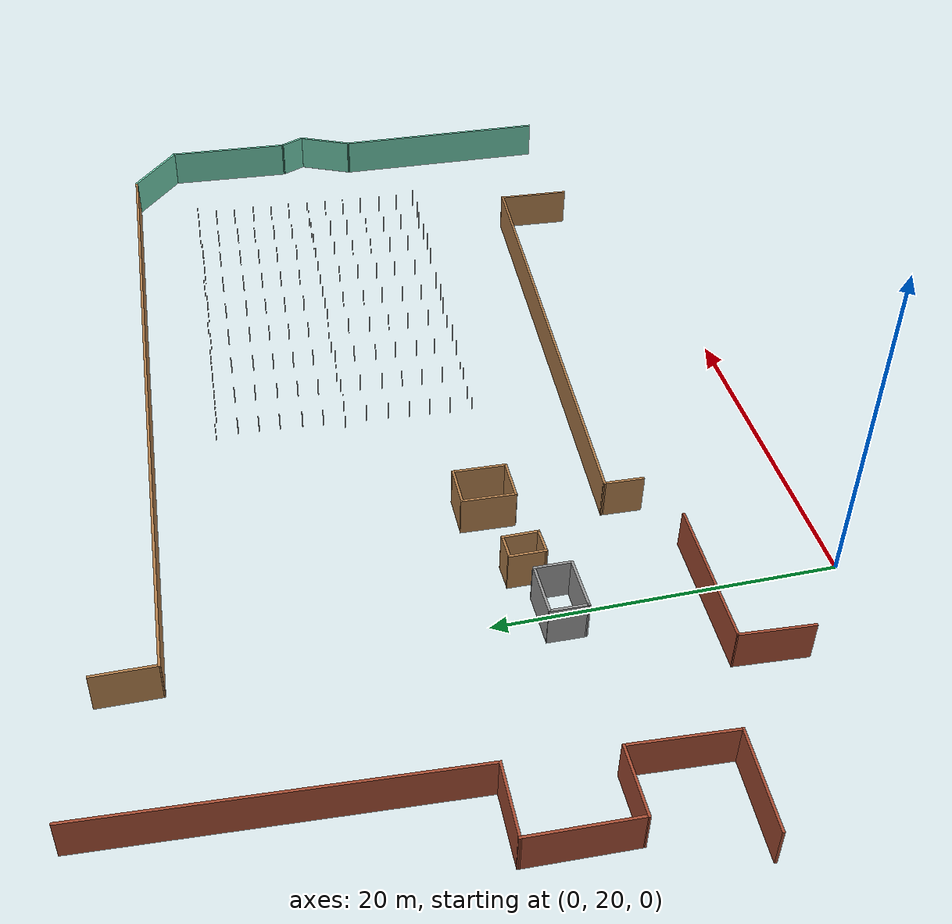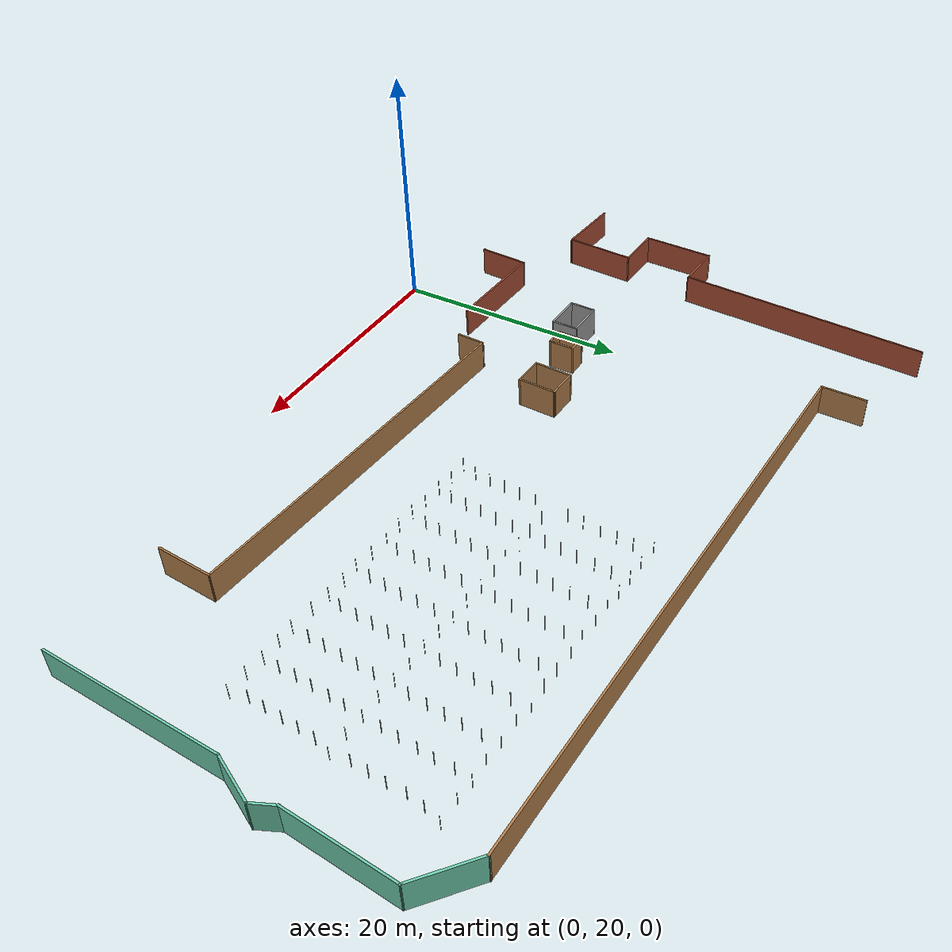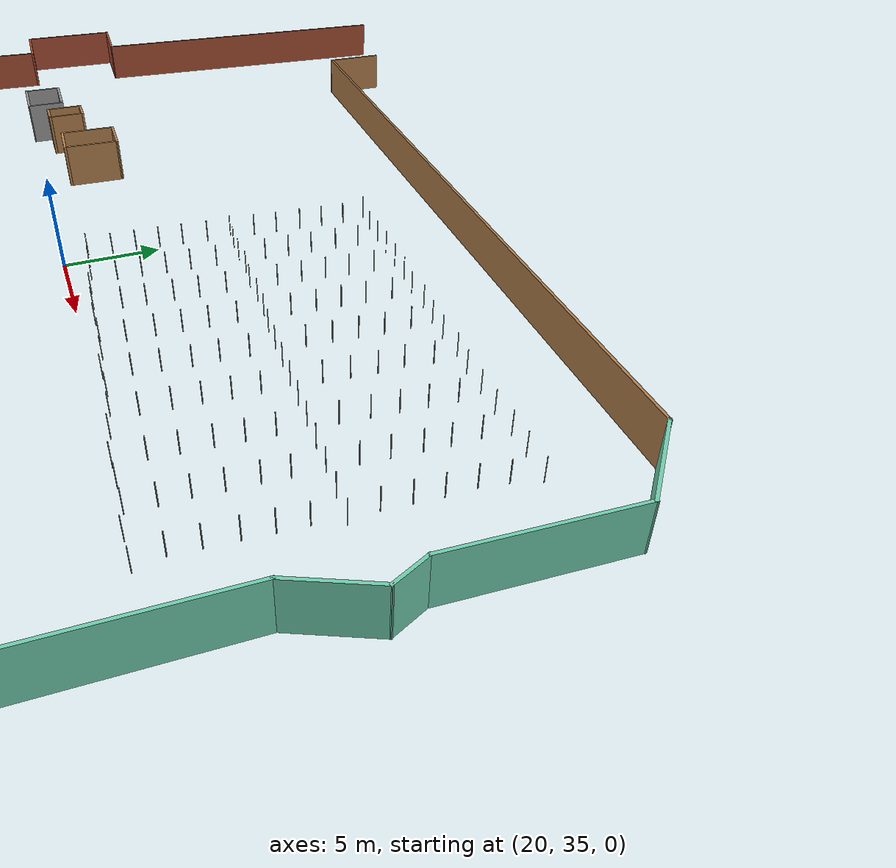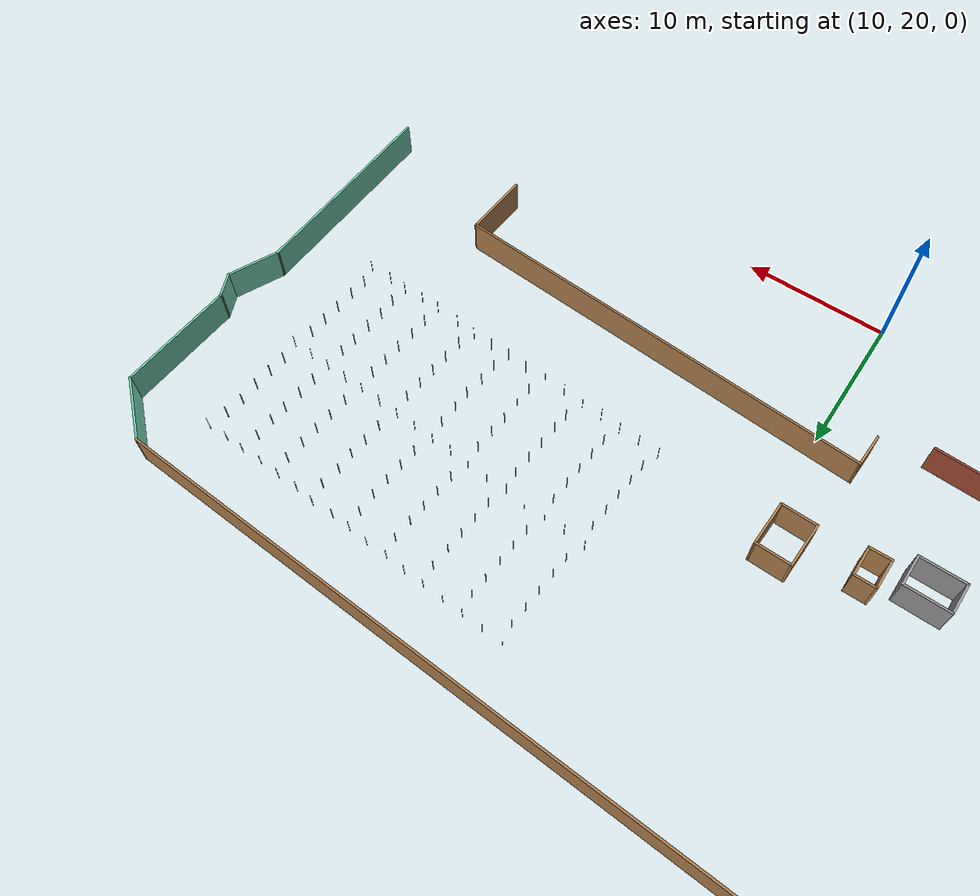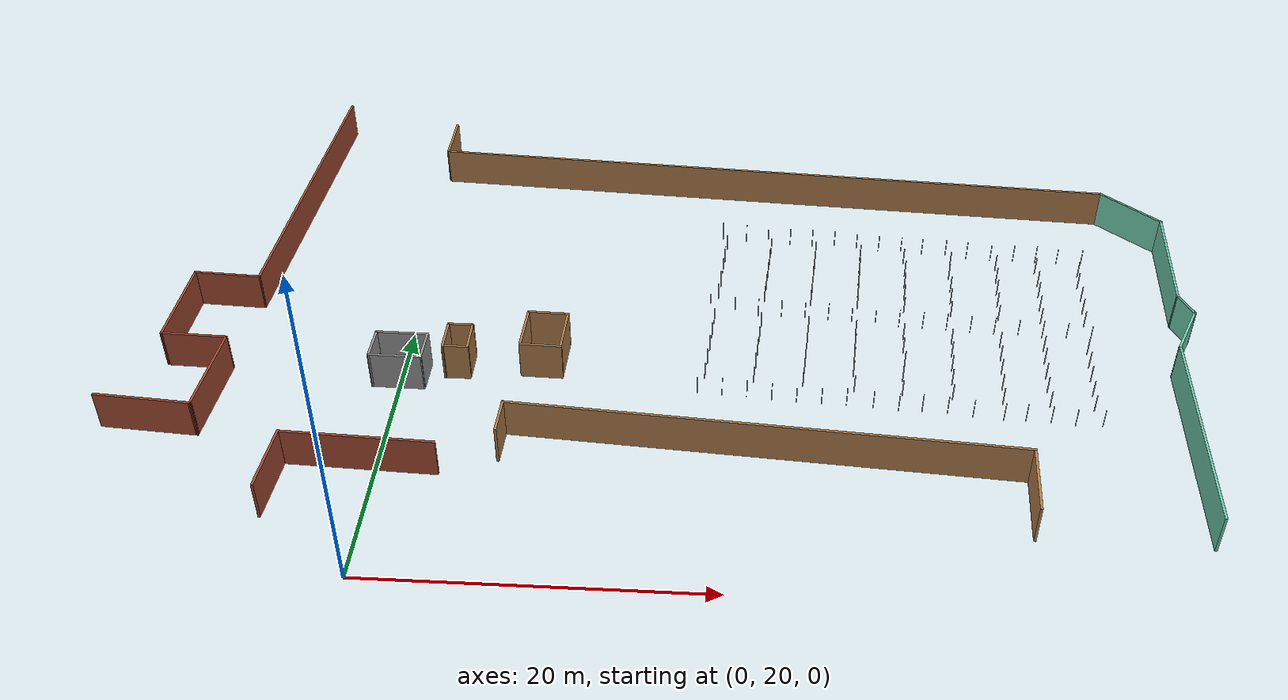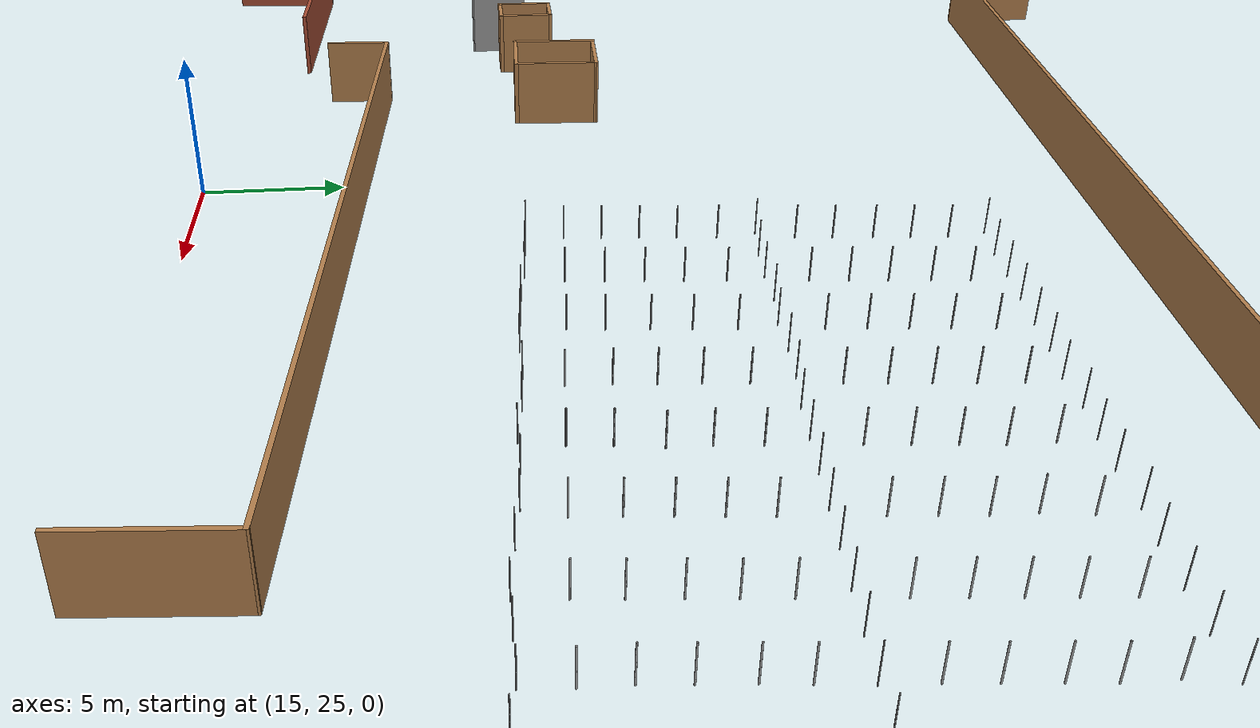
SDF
<sdf version="1.4">
 <world name="default">
  <model name="pole_0">
   <static>1</static>
   <pose>18.3 37.7 0.0 0.0 0.0 0.0</pose>
   <link name="link">
    <inertial>
     <mass>1</mass>
     <inertia><ixz>0</ixz><ixx>1</ixx><ixy>0</ixy><izz>1</izz><iyy>1</iyy><iyz>0</iyz></inertia>
    </inertial>
    <collision name="collision">
     <geometry><cylinder><length>1.27</length><radius>0.025</radius></cylinder></geometry>
    </collision>
    <visual name="visual">
     <geometry><cylinder><length>1.27</length><radius>0.025</radius></cylinder></geometry>
     <material>
      <script><uri>file://media/materials/scripts/gazebo.material</uri><name>Gazebo/Grey</name></script>
     </material>
    </visual>
    <velocity_decay><linear>0</linear><angular>0</angular></velocity_decay>
   </link>
  </model>
  <model name="pole_1">
   <static>1</static>
   <pose>21.3 37.5 0.0 0.0 0.0 0.0</pose>
   <link name="link">
    <inertial>
     <mass>1</mass>
     <inertia><ixz>0</ixz><ixx>1</ixx><ixy>0</ixy><izz>1</izz><iyy>1</iyy><iyz>0</iyz></inertia>
    </inertial>
    <collision name="collision">
     <geometry><cylinder><length>1.27</length><radius>0.025</radius></cylinder></geometry>
    </collision>
    <visual name="visual">
     <geometry><cylinder><length>1.27</length><radius>0.025</radius></cylinder></geometry>
     <material>
      <script><uri>file://media/materials/scripts/gazebo.material</uri><name>Gazebo/Grey</name></script>
     </material>
    </visual>
    <velocity_decay><linear>0</linear><angular>0</angular></velocity_decay>
   </link>
  </model>
  <model name="pole_2">
   <static>1</static>
   <pose>24.3 37.3 0.0 0.0 0.0 0.0</pose>
   <link name="link">
    <inertial>
     <mass>1</mass>
     <inertia><ixz>0</ixz><ixx>1</ixx><ixy>0</ixy><izz>1</izz><iyy>1</iyy><iyz>0</iyz></inertia>
    </inertial>
    <collision name="collision">
     <geometry><cylinder><length>1.27</length><radius>0.025</radius></cylinder></geometry>
    </collision>
    <visual name="visual">
     <geometry><cylinder><length>1.27</length><radius>0.025</radius></cylinder></geometry>
     <material>
      <script><uri>file://media/materials/scripts/gazebo.material</uri><name>Gazebo/Grey</name></script>
     </material>
    </visual>
    <velocity_decay><linear>0</linear><angular>0</angular></velocity_decay>
   </link>
  </model>
  <model name="pole_3">
   <static>1</static>
   <pose>27.4 37.0 0.0 0.0 0.0 0.0</pose>
   <link name="link">
    <inertial>
     <mass>1</mass>
     <inertia><ixz>0</ixz><ixx>1</ixx><ixy>0</ixy><izz>1</izz><iyy>1</iyy><iyz>0</iyz></inertia>
    </inertial>
    <collision name="collision">
     <geometry><cylinder><length>1.27</length><radius>0.025</radius></cylinder></geometry>
    </collision>
    <visual name="visual">
     <geometry><cylinder><length>1.27</length><radius>0.025</radius></cylinder></geometry>
     <material>
      <script><uri>file://media/materials/scripts/gazebo.material</uri><name>Gazebo/Grey</name></script>
     </material>
    </visual>
    <velocity_decay><linear>0</linear><angular>0</angular></velocity_decay>
   </link>
  </model>
  <model name="pole_4">
   <static>1</static>
   <pose>30.3 36.8 0.0 0.0 0.0 0.0</pose>
   <link name="link">
    <inertial>
     <mass>1</mass>
     <inertia><ixz>0</ixz><ixx>1</ixx><ixy>0</ixy><izz>1</izz><iyy>1</iyy><iyz>0</iyz></inertia>
    </inertial>
    <collision name="collision">
     <geometry><cylinder><length>1.27</length><radius>0.025</radius></cylinder></geometry>
    </collision>
    <visual name="visual">
     <geometry><cylinder><length>1.27</length><radius>0.025</radius></cylinder></geometry>
     <material>
      <script><uri>file://media/materials/scripts/gazebo.material</uri><name>Gazebo/Grey</name></script>
     </material>
    </visual>
    <velocity_decay><linear>0</linear><angular>0</angular></velocity_decay>
   </link>
  </model>
  <model name="pole_5">
   <static>1</static>
   <pose>33.3 36.6 0.0 0.0 0.0 0.0</pose>
   <link name="link">
    <inertial>
     <mass>1</mass>
     <inertia><ixz>0</ixz><ixx>1</ixx><ixy>0</ixy><izz>1</izz><iyy>1</iyy><iyz>0</iyz></inertia>
    </inertial>
    <collision name="collision">
     <geometry><cylinder><length>1.27</length><radius>0.025</radius></cylinder></geometry>
    </collision>
    <visual name="visual">
     <geometry><cylinder><length>1.27</length><radius>0.025</radius></cylinder></geometry>
     <material>
      <script><uri>file://media/materials/scripts/gazebo.material</uri><name>Gazebo/Grey</name></script>
     </material>
    </visual>
    <velocity_decay><linear>0</linear><angular>0</angular></velocity_decay>
   </link>
  </model>
  <model name="pole_6">
   <static>1</static>
   <pose>36.3 36.4 0.0 0.0 0.0 0.0</pose>
   <link name="link">
    <inertial>
     <mass>1</mass>
     <inertia><ixz>0</ixz><ixx>1</ixx><ixy>0</ixy><izz>1</izz><iyy>1</iyy><iyz>0</iyz></inertia>
    </inertial>
    <collision name="collision">
     <geometry><cylinder><length>1.27</length><radius>0.025</radius></cylinder></geometry>
    </collision>
    <visual name="visual">
     <geometry><cylinder><length>1.27</length><radius>0.025</radius></cylinder></geometry>
     <material>
      <script><uri>file://media/materials/scripts/gazebo.material</uri><name>Gazebo/Grey</name></script>
     </material>
    </visual>
    <velocity_decay><linear>0</linear><angular>0</angular></velocity_decay>
   </link>
  </model>
  <model name="pole_7">
   <static>1</static>
   <pose>39.1 36.3 0.0 0.0 0.0 0.0</pose>
   <link name="link">
    <inertial>
     <mass>1</mass>
     <inertia><ixz>0</ixz><ixx>1</ixx><ixy>0</ixy><izz>1</izz><iyy>1</iyy><iyz>0</iyz></inertia>
    </inertial>
    <collision name="collision">
     <geometry><cylinder><length>1.27</length><radius>0.025</radius></cylinder></geometry>
    </collision>
    <visual name="visual">
     <geometry><cylinder><length>1.27</length><radius>0.025</radius></cylinder></geometry>
     <material>
      <script><uri>file://media/materials/scripts/gazebo.material</uri><name>Gazebo/Grey</name></script>
     </material>
    </visual>
    <velocity_decay><linear>0</linear><angular>0</angular></velocity_decay>
   </link>
  </model>
  <model name="pole_8">
   <static>1</static>
   <pose>41.7 36.1 0.0 0.0 0.0 0.0</pose>
   <link name="link">
    <inertial>
     <mass>1</mass>
     <inertia><ixz>0</ixz><ixx>1</ixx><ixy>0</ixy><izz>1</izz><iyy>1</iyy><iyz>0</iyz></inertia>
    </inertial>
    <collision name="collision">
     <geometry><cylinder><length>1.27</length><radius>0.025</radius></cylinder></geometry>
    </collision>
    <visual name="visual">
     <geometry><cylinder><length>1.27</length><radius>0.025</radius></cylinder></geometry>
     <material>
      <script><uri>file://media/materials/scripts/gazebo.material</uri><name>Gazebo/Grey</name></script>
     </material>
    </visual>
    <velocity_decay><linear>0</linear><angular>0</angular></velocity_decay>
   </link>
  </model>
  <model name="pole_9">
   <static>1</static>
   <pose>18.4 39.0 0.0 0.0 0.0 0.0</pose>
   <link name="link">
    <inertial>
     <mass>1</mass>
     <inertia><ixz>0</ixz><ixx>1</ixx><ixy>0</ixy><izz>1</izz><iyy>1</iyy><iyz>0</iyz></inertia>
    </inertial>
    <collision name="collision">
     <geometry><cylinder><length>1.27</length><radius>0.025</radius></cylinder></geometry>
    </collision>
    <visual name="visual">
     <geometry><cylinder><length>1.27</length><radius>0.025</radius></cylinder></geometry>
     <material>
      <script><uri>file://media/materials/scripts/gazebo.material</uri><name>Gazebo/Grey</name></script>
     </material>
    </visual>
    <velocity_decay><linear>0</linear><angular>0</angular></velocity_decay>
   </link>
  </model>
  <model name="pole_10">
   <static>1</static>
   <pose>21.4 38.8 0.0 0.0 0.0 0.0</pose>
   <link name="link">
    <inertial>
     <mass>1</mass>
     <inertia><ixz>0</ixz><ixx>1</ixx><ixy>0</ixy><izz>1</izz><iyy>1</iyy><iyz>0</iyz></inertia>
    </inertial>
    <collision name="collision">
     <geometry><cylinder><length>1.27</length><radius>0.025</radius></cylinder></geometry>
    </collision>
    <visual name="visual">
     <geometry><cylinder><length>1.27</length><radius>0.025</radius></cylinder></geometry>
     <material>
      <script><uri>file://media/materials/scripts/gazebo.material</uri><name>Gazebo/Grey</name></script>
     </material>
    </visual>
    <velocity_decay><linear>0</linear><angular>0</angular></velocity_decay>
   </link>
  </model>
  <model name="pole_11">
   <static>1</static>
   <pose>24.4 38.5 0.0 0.0 0.0 0.0</pose>
   <link name="link">
    <inertial>
     <mass>1</mass>
     <inertia><ixz>0</ixz><ixx>1</ixx><ixy>0</ixy><izz>1</izz><iyy>1</iyy><iyz>0</iyz></inertia>
    </inertial>
    <collision name="collision">
     <geometry><cylinder><length>1.27</length><radius>0.025</radius></cylinder></geometry>
    </collision>
    <visual name="visual">
     <geometry><cylinder><length>1.27</length><radius>0.025</radius></cylinder></geometry>
     <material>
      <script><uri>file://media/materials/scripts/gazebo.material</uri><name>Gazebo/Grey</name></script>
     </material>
    </visual>
    <velocity_decay><linear>0</linear><angular>0</angular></velocity_decay>
   </link>
  </model>
  <model name="pole_12">
   <static>1</static>
   <pose>27.4 38.4 0.0 0.0 0.0 0.0</pose>
   <link name="link">
    <inertial>
     <mass>1</mass>
     <inertia><ixz>0</ixz><ixx>1</ixx><ixy>0</ixy><izz>1</izz><iyy>1</iyy><iyz>0</iyz></inertia>
    </inertial>
    <collision name="collision">
     <geometry><cylinder><length>1.27</length><radius>0.025</radius></cylinder></geometry>
    </collision>
    <visual name="visual">
     <geometry><cylinder><length>1.27</length><radius>0.025</radius></cylinder></geometry>
     <material>
      <script><uri>file://media/materials/scripts/gazebo.material</uri><name>Gazebo/Grey</name></script>
     </material>
    </visual>
    <velocity_decay><linear>0</linear><angular>0</angular></velocity_decay>
   </link>
  </model>
  <model name="pole_13">
   <static>1</static>
   <pose>30.4 38.1 0.0 0.0 0.0 0.0</pose>
   <link name="link">
    <inertial>
     <mass>1</mass>
     <inertia><ixz>0</ixz><ixx>1</ixx><ixy>0</ixy><izz>1</izz><iyy>1</iyy><iyz>0</iyz></inertia>
    </inertial>
    <collision name="collision">
     <geometry><cylinder><length>1.27</length><radius>0.025</radius></cylinder></geometry>
    </collision>
    <visual name="visual">
     <geometry><cylinder><length>1.27</length><radius>0.025</radius></cylinder></geometry>
     <material>
      <script><uri>file://media/materials/scripts/gazebo.material</uri><name>Gazebo/Grey</name></script>
     </material>
    </visual>
    <velocity_decay><linear>0</linear><angular>0</angular></velocity_decay>
   </link>
  </model>
  <model name="pole_14">
   <static>1</static>
   <pose>33.4 38.0 0.0 0.0 0.0 0.0</pose>
   <link name="link">
    <inertial>
     <mass>1</mass>
     <inertia><ixz>0</ixz><ixx>1</ixx><ixy>0</ixy><izz>1</izz><iyy>1</iyy><iyz>0</iyz></inertia>
    </inertial>
    <collision name="collision">
     <geometry><cylinder><length>1.27</length><radius>0.025</radius></cylinder></geometry>
    </collision>
    <visual name="visual">
     <geometry><cylinder><length>1.27</length><radius>0.025</radius></cylinder></geometry>
     <material>
      <script><uri>file://media/materials/scripts/gazebo.material</uri><name>Gazebo/Grey</name></script>
     </material>
    </visual>
    <velocity_decay><linear>0</linear><angular>0</angular></velocity_decay>
   </link>
  </model>
  <model name="pole_15">
   <static>1</static>
   <pose>36.4 37.7 0.0 0.0 0.0 0.0</pose>
   <link name="link">
    <inertial>
     <mass>1</mass>
     <inertia><ixz>0</ixz><ixx>1</ixx><ixy>0</ixy><izz>1</izz><iyy>1</iyy><iyz>0</iyz></inertia>
    </inertial>
    <collision name="collision">
     <geometry><cylinder><length>1.27</length><radius>0.025</radius></cylinder></geometry>
    </collision>
    <visual name="visual">
     <geometry><cylinder><length>1.27</length><radius>0.025</radius></cylinder></geometry>
     <material>
      <script><uri>file://media/materials/scripts/gazebo.material</uri><name>Gazebo/Grey</name></script>
     </material>
    </visual>
    <velocity_decay><linear>0</linear><angular>0</angular></velocity_decay>
   </link>
  </model>
  <model name="pole_16">
   <static>1</static>
   <pose>39.1 37.6 0.0 0.0 0.0 0.0</pose>
   <link name="link">
    <inertial>
     <mass>1</mass>
     <inertia><ixz>0</ixz><ixx>1</ixx><ixy>0</ixy><izz>1</izz><iyy>1</iyy><iyz>0</iyz></inertia>
    </inertial>
    <collision name="collision">
     <geometry><cylinder><length>1.27</length><radius>0.025</radius></cylinder></geometry>
    </collision>
    <visual name="visual">
     <geometry><cylinder><length>1.27</length><radius>0.025</radius></cylinder></geometry>
     <material>
      <script><uri>file://media/materials/scripts/gazebo.material</uri><name>Gazebo/Grey</name></script>
     </material>
    </visual>
    <velocity_decay><linear>0</linear><angular>0</angular></velocity_decay>
   </link>
  </model>
  <model name="pole_17">
   <static>1</static>
   <pose>41.8 37.4 0.0 0.0 0.0 0.0</pose>
   <link name="link">
    <inertial>
     <mass>1</mass>
     <inertia><ixz>0</ixz><ixx>1</ixx><ixy>0</ixy><izz>1</izz><iyy>1</iyy><iyz>0</iyz></inertia>
    </inertial>
    <collision name="collision">
     <geometry><cylinder><length>1.27</length><radius>0.025</radius></cylinder></geometry>
    </collision>
    <visual name="visual">
     <geometry><cylinder><length>1.27</length><radius>0.025</radius></cylinder></geometry>
     <material>
      <script><uri>file://media/materials/scripts/gazebo.material</uri><name>Gazebo/Grey</name></script>
     </material>
    </visual>
    <velocity_decay><linear>0</linear><angular>0</angular></velocity_decay>
   </link>
  </model>
  <model name="pole_18">
   <static>1</static>
   <pose>18.5 40.3 0.0 0.0 0.0 0.0</pose>
   <link name="link">
    <inertial>
     <mass>1</mass>
     <inertia><ixz>0</ixz><ixx>1</ixx><ixy>0</ixy><izz>1</izz><iyy>1</iyy><iyz>0</iyz></inertia>
    </inertial>
    <collision name="collision">
     <geometry><cylinder><length>1.27</length><radius>0.025</radius></cylinder></geometry>
    </collision>
    <visual name="visual">
     <geometry><cylinder><length>1.27</length><radius>0.025</radius></cylinder></geometry>
     <material>
      <script><uri>file://media/materials/scripts/gazebo.material</uri><name>Gazebo/Grey</name></script>
     </material>
    </visual>
    <velocity_decay><linear>0</linear><angular>0</angular></velocity_decay>
   </link>
  </model>
  <model name="pole_19">
   <static>1</static>
   <pose>21.5 40.1 0.0 0.0 0.0 0.0</pose>
   <link name="link">
    <inertial>
     <mass>1</mass>
     <inertia><ixz>0</ixz><ixx>1</ixx><ixy>0</ixy><izz>1</izz><iyy>1</iyy><iyz>0</iyz></inertia>
    </inertial>
    <collision name="collision">
     <geometry><cylinder><length>1.27</length><radius>0.025</radius></cylinder></geometry>
    </collision>
    <visual name="visual">
     <geometry><cylinder><length>1.27</length><radius>0.025</radius></cylinder></geometry>
     <material>
      <script><uri>file://media/materials/scripts/gazebo.material</uri><name>Gazebo/Grey</name></script>
     </material>
    </visual>
    <velocity_decay><linear>0</linear><angular>0</angular></velocity_decay>
   </link>
  </model>
  <model name="pole_20">
   <static>1</static>
   <pose>24.5 39.9 0.0 0.0 0.0 0.0</pose>
   <link name="link">
    <inertial>
     <mass>1</mass>
     <inertia><ixz>0</ixz><ixx>1</ixx><ixy>0</ixy><izz>1</izz><iyy>1</iyy><iyz>0</iyz></inertia>
    </inertial>
    <collision name="collision">
     <geometry><cylinder><length>1.27</length><radius>0.025</radius></cylinder></geometry>
    </collision>
    <visual name="visual">
     <geometry><cylinder><length>1.27</length><radius>0.025</radius></cylinder></geometry>
     <material>
      <script><uri>file://media/materials/scripts/gazebo.material</uri><name>Gazebo/Grey</name></script>
     </material>
    </visual>
    <velocity_decay><linear>0</linear><angular>0</angular></velocity_decay>
   </link>
  </model>
  <model name="pole_21">
   <static>1</static>
   <pose>27.5 39.7 0.0 0.0 0.0 0.0</pose>
   <link name="link">
    <inertial>
     <mass>1</mass>
     <inertia><ixz>0</ixz><ixx>1</ixx><ixy>0</ixy><izz>1</izz><iyy>1</iyy><iyz>0</iyz></inertia>
    </inertial>
    <collision name="collision">
     <geometry><cylinder><length>1.27</length><radius>0.025</radius></cylinder></geometry>
    </collision>
    <visual name="visual">
     <geometry><cylinder><length>1.27</length><radius>0.025</radius></cylinder></geometry>
     <material>
      <script><uri>file://media/materials/scripts/gazebo.material</uri><name>Gazebo/Grey</name></script>
     </material>
    </visual>
    <velocity_decay><linear>0</linear><angular>0</angular></velocity_decay>
   </link>
  </model>
  <model name="pole_22">
   <static>1</static>
   <pose>30.6 39.5 0.0 0.0 0.0 0.0</pose>
   <link name="link">
    <inertial>
     <mass>1</mass>
     <inertia><ixz>0</ixz><ixx>1</ixx><ixy>0</ixy><izz>1</izz><iyy>1</iyy><iyz>0</iyz></inertia>
    </inertial>
    <collision name="collision">
     <geometry><cylinder><length>1.27</length><radius>0.025</radius></cylinder></geometry>
    </collision>
    <visual name="visual">
     <geometry><cylinder><length>1.27</length><radius>0.025</radius></cylinder></geometry>
     <material>
      <script><uri>file://media/materials/scripts/gazebo.material</uri><name>Gazebo/Grey</name></script>
     </material>
    </visual>
    <velocity_decay><linear>0</linear><angular>0</angular></velocity_decay>
   </link>
  </model>
  <model name="pole_23">
   <static>1</static>
   <pose>33.5 39.3 0.0 0.0 0.0 0.0</pose>
   <link name="link">
    <inertial>
     <mass>1</mass>
     <inertia><ixz>0</ixz><ixx>1</ixx><ixy>0</ixy><izz>1</izz><iyy>1</iyy><iyz>0</iyz></inertia>
    </inertial>
    <collision name="collision">
     <geometry><cylinder><length>1.27</length><radius>0.025</radius></cylinder></geometry>
    </collision>
    <visual name="visual">
     <geometry><cylinder><length>1.27</length><radius>0.025</radius></cylinder></geometry>
     <material>
      <script><uri>file://media/materials/scripts/gazebo.material</uri><name>Gazebo/Grey</name></script>
     </material>
    </visual>
    <velocity_decay><linear>0</linear><angular>0</angular></velocity_decay>
   </link>
  </model>
  <model name="pole_24">
   <static>1</static>
   <pose>36.5 39.1 0.0 0.0 0.0 0.0</pose>
   <link name="link">
    <inertial>
     <mass>1</mass>
     <inertia><ixz>0</ixz><ixx>1</ixx><ixy>0</ixy><izz>1</izz><iyy>1</iyy><iyz>0</iyz></inertia>
    </inertial>
    <collision name="collision">
     <geometry><cylinder><length>1.27</length><radius>0.025</radius></cylinder></geometry>
    </collision>
    <visual name="visual">
     <geometry><cylinder><length>1.27</length><radius>0.025</radius></cylinder></geometry>
     <material>
      <script><uri>file://media/materials/scripts/gazebo.material</uri><name>Gazebo/Grey</name></script>
     </material>
    </visual>
    <velocity_decay><linear>0</linear><angular>0</angular></velocity_decay>
   </link>
  </model>
  <model name="pole_25">
   <static>1</static>
   <pose>39.2 38.9 0.0 0.0 0.0 0.0</pose>
   <link name="link">
    <inertial>
     <mass>1</mass>
     <inertia><ixz>0</ixz><ixx>1</ixx><ixy>0</ixy><izz>1</izz><iyy>1</iyy><iyz>0</iyz></inertia>
    </inertial>
    <collision name="collision">
     <geometry><cylinder><length>1.27</length><radius>0.025</radius></cylinder></geometry>
    </collision>
    <visual name="visual">
     <geometry><cylinder><length>1.27</length><radius>0.025</radius></cylinder></geometry>
     <material>
      <script><uri>file://media/materials/scripts/gazebo.material</uri><name>Gazebo/Grey</name></script>
     </material>
    </visual>
    <velocity_decay><linear>0</linear><angular>0</angular></velocity_decay>
   </link>
  </model>
  <model name="pole_26">
   <static>1</static>
   <pose>41.9 38.8 0.0 0.0 0.0 0.0</pose>
   <link name="link">
    <inertial>
     <mass>1</mass>
     <inertia><ixz>0</ixz><ixx>1</ixx><ixy>0</ixy><izz>1</izz><iyy>1</iyy><iyz>0</iyz></inertia>
    </inertial>
    <collision name="collision">
     <geometry><cylinder><length>1.27</length><radius>0.025</radius></cylinder></geometry>
    </collision>
    <visual name="visual">
     <geometry><cylinder><length>1.27</length><radius>0.025</radius></cylinder></geometry>
     <material>
      <script><uri>file://media/materials/scripts/gazebo.material</uri><name>Gazebo/Grey</name></script>
     </material>
    </visual>
    <velocity_decay><linear>0</linear><angular>0</angular></velocity_decay>
   </link>
  </model>
  <model name="pole_27">
   <static>1</static>
   <pose>18.6 41.6 0.0 0.0 0.0 0.0</pose>
   <link name="link">
    <inertial>
     <mass>1</mass>
     <inertia><ixz>0</ixz><ixx>1</ixx><ixy>0</ixy><izz>1</izz><iyy>1</iyy><iyz>0</iyz></inertia>
    </inertial>
    <collision name="collision">
     <geometry><cylinder><length>1.27</length><radius>0.025</radius></cylinder></geometry>
    </collision>
    <visual name="visual">
     <geometry><cylinder><length>1.27</length><radius>0.025</radius></cylinder></geometry>
     <material>
      <script><uri>file://media/materials/scripts/gazebo.material</uri><name>Gazebo/Grey</name></script>
     </material>
    </visual>
    <velocity_decay><linear>0</linear><angular>0</angular></velocity_decay>
   </link>
  </model>
  <model name="pole_28">
   <static>1</static>
   <pose>21.6 41.4 0.0 0.0 0.0 0.0</pose>
   <link name="link">
    <inertial>
     <mass>1</mass>
     <inertia><ixz>0</ixz><ixx>1</ixx><ixy>0</ixy><izz>1</izz><iyy>1</iyy><iyz>0</iyz></inertia>
    </inertial>
    <collision name="collision">
     <geometry><cylinder><length>1.27</length><radius>0.025</radius></cylinder></geometry>
    </collision>
    <visual name="visual">
     <geometry><cylinder><length>1.27</length><radius>0.025</radius></cylinder></geometry>
     <material>
      <script><uri>file://media/materials/scripts/gazebo.material</uri><name>Gazebo/Grey</name></script>
     </material>
    </visual>
    <velocity_decay><linear>0</linear><angular>0</angular></velocity_decay>
   </link>
  </model>
  <model name="pole_29">
   <static>1</static>
   <pose>24.6 41.2 0.0 0.0 0.0 0.0</pose>
   <link name="link">
    <inertial>
     <mass>1</mass>
     <inertia><ixz>0</ixz><ixx>1</ixx><ixy>0</ixy><izz>1</izz><iyy>1</iyy><iyz>0</iyz></inertia>
    </inertial>
    <collision name="collision">
     <geometry><cylinder><length>1.27</length><radius>0.025</radius></cylinder></geometry>
    </collision>
    <visual name="visual">
     <geometry><cylinder><length>1.27</length><radius>0.025</radius></cylinder></geometry>
     <material>
      <script><uri>file://media/materials/scripts/gazebo.material</uri><name>Gazebo/Grey</name></script>
     </material>
    </visual>
    <velocity_decay><linear>0</linear><angular>0</angular></velocity_decay>
   </link>
  </model>
  <model name="pole_30">
   <static>1</static>
   <pose>27.6 41.0 0.0 0.0 0.0 0.0</pose>
   <link name="link">
    <inertial>
     <mass>1</mass>
     <inertia><ixz>0</ixz><ixx>1</ixx><ixy>0</ixy><izz>1</izz><iyy>1</iyy><iyz>0</iyz></inertia>
    </inertial>
    <collision name="collision">
     <geometry><cylinder><length>1.27</length><radius>0.025</radius></cylinder></geometry>
    </collision>
    <visual name="visual">
     <geometry><cylinder><length>1.27</length><radius>0.025</radius></cylinder></geometry>
     <material>
      <script><uri>file://media/materials/scripts/gazebo.material</uri><name>Gazebo/Grey</name></script>
     </material>
    </visual>
    <velocity_decay><linear>0</linear><angular>0</angular></velocity_decay>
   </link>
  </model>
  <model name="pole_31">
   <static>1</static>
   <pose>30.6 40.8 0.0 0.0 0.0 0.0</pose>
   <link name="link">
    <inertial>
     <mass>1</mass>
     <inertia><ixz>0</ixz><ixx>1</ixx><ixy>0</ixy><izz>1</izz><iyy>1</iyy><iyz>0</iyz></inertia>
    </inertial>
    <collision name="collision">
     <geometry><cylinder><length>1.27</length><radius>0.025</radius></cylinder></geometry>
    </collision>
    <visual name="visual">
     <geometry><cylinder><length>1.27</length><radius>0.025</radius></cylinder></geometry>
     <material>
      <script><uri>file://media/materials/scripts/gazebo.material</uri><name>Gazebo/Grey</name></script>
     </material>
    </visual>
    <velocity_decay><linear>0</linear><angular>0</angular></velocity_decay>
   </link>
  </model>
  <model name="pole_32">
   <static>1</static>
   <pose>33.6 40.6 0.0 0.0 0.0 0.0</pose>
   <link name="link">
    <inertial>
     <mass>1</mass>
     <inertia><ixz>0</ixz><ixx>1</ixx><ixy>0</ixy><izz>1</izz><iyy>1</iyy><iyz>0</iyz></inertia>
    </inertial>
    <collision name="collision">
     <geometry><cylinder><length>1.27</length><radius>0.025</radius></cylinder></geometry>
    </collision>
    <visual name="visual">
     <geometry><cylinder><length>1.27</length><radius>0.025</radius></cylinder></geometry>
     <material>
      <script><uri>file://media/materials/scripts/gazebo.material</uri><name>Gazebo/Grey</name></script>
     </material>
    </visual>
    <velocity_decay><linear>0</linear><angular>0</angular></velocity_decay>
   </link>
  </model>
  <model name="pole_33">
   <static>1</static>
   <pose>36.6 40.4 0.0 0.0 0.0 0.0</pose>
   <link name="link">
    <inertial>
     <mass>1</mass>
     <inertia><ixz>0</ixz><ixx>1</ixx><ixy>0</ixy><izz>1</izz><iyy>1</iyy><iyz>0</iyz></inertia>
    </inertial>
    <collision name="collision">
     <geometry><cylinder><length>1.27</length><radius>0.025</radius></cylinder></geometry>
    </collision>
    <visual name="visual">
     <geometry><cylinder><length>1.27</length><radius>0.025</radius></cylinder></geometry>
     <material>
      <script><uri>file://media/materials/scripts/gazebo.material</uri><name>Gazebo/Grey</name></script>
     </material>
    </visual>
    <velocity_decay><linear>0</linear><angular>0</angular></velocity_decay>
   </link>
  </model>
  <model name="pole_34">
   <static>1</static>
   <pose>39.3 40.3 0.0 0.0 0.0 0.0</pose>
   <link name="link">
    <inertial>
     <mass>1</mass>
     <inertia><ixz>0</ixz><ixx>1</ixx><ixy>0</ixy><izz>1</izz><iyy>1</iyy><iyz>0</iyz></inertia>
    </inertial>
    <collision name="collision">
     <geometry><cylinder><length>1.27</length><radius>0.025</radius></cylinder></geometry>
    </collision>
    <visual name="visual">
     <geometry><cylinder><length>1.27</length><radius>0.025</radius></cylinder></geometry>
     <material>
      <script><uri>file://media/materials/scripts/gazebo.material</uri><name>Gazebo/Grey</name></script>
     </material>
    </visual>
    <velocity_decay><linear>0</linear><angular>0</angular></velocity_decay>
   </link>
  </model>
  <model name="pole_35">
   <static>1</static>
   <pose>42.0 40.1 0.0 0.0 0.0 0.0</pose>
   <link name="link">
    <inertial>
     <mass>1</mass>
     <inertia><ixz>0</ixz><ixx>1</ixx><ixy>0</ixy><izz>1</izz><iyy>1</iyy><iyz>0</iyz></inertia>
    </inertial>
    <collision name="collision">
     <geometry><cylinder><length>1.27</length><radius>0.025</radius></cylinder></geometry>
    </collision>
    <visual name="visual">
     <geometry><cylinder><length>1.27</length><radius>0.025</radius></cylinder></geometry>
     <material>
      <script><uri>file://media/materials/scripts/gazebo.material</uri><name>Gazebo/Grey</name></script>
     </material>
    </visual>
    <velocity_decay><linear>0</linear><angular>0</angular></velocity_decay>
   </link>
  </model>
  <model name="pole_36">
   <static>1</static>
   <pose>18.7 43.0 0.0 0.0 0.0 0.0</pose>
   <link name="link">
    <inertial>
     <mass>1</mass>
     <inertia><ixz>0</ixz><ixx>1</ixx><ixy>0</ixy><izz>1</izz><iyy>1</iyy><iyz>0</iyz></inertia>
    </inertial>
    <collision name="collision">
     <geometry><cylinder><length>1.27</length><radius>0.025</radius></cylinder></geometry>
    </collision>
    <visual name="visual">
     <geometry><cylinder><length>1.27</length><radius>0.025</radius></cylinder></geometry>
     <material>
      <script><uri>file://media/materials/scripts/gazebo.material</uri><name>Gazebo/Grey</name></script>
     </material>
    </visual>
    <velocity_decay><linear>0</linear><angular>0</angular></velocity_decay>
   </link>
  </model>
  <model name="pole_37">
   <static>1</static>
   <pose>21.7 42.8 0.0 0.0 0.0 0.0</pose>
   <link name="link">
    <inertial>
     <mass>1</mass>
     <inertia><ixz>0</ixz><ixx>1</ixx><ixy>0</ixy><izz>1</izz><iyy>1</iyy><iyz>0</iyz></inertia>
    </inertial>
    <collision name="collision">
     <geometry><cylinder><length>1.27</length><radius>0.025</radius></cylinder></geometry>
    </collision>
    <visual name="visual">
     <geometry><cylinder><length>1.27</length><radius>0.025</radius></cylinder></geometry>
     <material>
      <script><uri>file://media/materials/scripts/gazebo.material</uri><name>Gazebo/Grey</name></script>
     </material>
    </visual>
    <velocity_decay><linear>0</linear><angular>0</angular></velocity_decay>
   </link>
  </model>
  <model name="pole_38">
   <static>1</static>
   <pose>24.7 42.6 0.0 0.0 0.0 0.0</pose>
   <link name="link">
    <inertial>
     <mass>1</mass>
     <inertia><ixz>0</ixz><ixx>1</ixx><ixy>0</ixy><izz>1</izz><iyy>1</iyy><iyz>0</iyz></inertia>
    </inertial>
    <collision name="collision">
     <geometry><cylinder><length>1.27</length><radius>0.025</radius></cylinder></geometry>
    </collision>
    <visual name="visual">
     <geometry><cylinder><length>1.27</length><radius>0.025</radius></cylinder></geometry>
     <material>
      <script><uri>file://media/materials/scripts/gazebo.material</uri><name>Gazebo/Grey</name></script>
     </material>
    </visual>
    <velocity_decay><linear>0</linear><angular>0</angular></velocity_decay>
   </link>
  </model>
  <model name="pole_39">
   <static>1</static>
   <pose>27.7 42.4 0.0 0.0 0.0 0.0</pose>
   <link name="link">
    <inertial>
     <mass>1</mass>
     <inertia><ixz>0</ixz><ixx>1</ixx><ixy>0</ixy><izz>1</izz><iyy>1</iyy><iyz>0</iyz></inertia>
    </inertial>
    <collision name="collision">
     <geometry><cylinder><length>1.27</length><radius>0.025</radius></cylinder></geometry>
    </collision>
    <visual name="visual">
     <geometry><cylinder><length>1.27</length><radius>0.025</radius></cylinder></geometry>
     <material>
      <script><uri>file://media/materials/scripts/gazebo.material</uri><name>Gazebo/Grey</name></script>
     </material>
    </visual>
    <velocity_decay><linear>0</linear><angular>0</angular></velocity_decay>
   </link>
  </model>
  <model name="pole_40">
   <static>1</static>
   <pose>30.7 42.2 0.0 0.0 0.0 0.0</pose>
   <link name="link">
    <inertial>
     <mass>1</mass>
     <inertia><ixz>0</ixz><ixx>1</ixx><ixy>0</ixy><izz>1</izz><iyy>1</iyy><iyz>0</iyz></inertia>
    </inertial>
    <collision name="collision">
     <geometry><cylinder><length>1.27</length><radius>0.025</radius></cylinder></geometry>
    </collision>
    <visual name="visual">
     <geometry><cylinder><length>1.27</length><radius>0.025</radius></cylinder></geometry>
     <material>
      <script><uri>file://media/materials/scripts/gazebo.material</uri><name>Gazebo/Grey</name></script>
     </material>
    </visual>
    <velocity_decay><linear>0</linear><angular>0</angular></velocity_decay>
   </link>
  </model>
  <model name="pole_41">
   <static>1</static>
   <pose>33.7 41.9 0.0 0.0 0.0 0.0</pose>
   <link name="link">
    <inertial>
     <mass>1</mass>
     <inertia><ixz>0</ixz><ixx>1</ixx><ixy>0</ixy><izz>1</izz><iyy>1</iyy><iyz>0</iyz></inertia>
    </inertial>
    <collision name="collision">
     <geometry><cylinder><length>1.27</length><radius>0.025</radius></cylinder></geometry>
    </collision>
    <visual name="visual">
     <geometry><cylinder><length>1.27</length><radius>0.025</radius></cylinder></geometry>
     <material>
      <script><uri>file://media/materials/scripts/gazebo.material</uri><name>Gazebo/Grey</name></script>
     </material>
    </visual>
    <velocity_decay><linear>0</linear><angular>0</angular></velocity_decay>
   </link>
  </model>
  <model name="pole_42">
   <static>1</static>
   <pose>36.7 41.7 0.0 0.0 0.0 0.0</pose>
   <link name="link">
    <inertial>
     <mass>1</mass>
     <inertia><ixz>0</ixz><ixx>1</ixx><ixy>0</ixy><izz>1</izz><iyy>1</iyy><iyz>0</iyz></inertia>
    </inertial>
    <collision name="collision">
     <geometry><cylinder><length>1.27</length><radius>0.025</radius></cylinder></geometry>
    </collision>
    <visual name="visual">
     <geometry><cylinder><length>1.27</length><radius>0.025</radius></cylinder></geometry>
     <material>
      <script><uri>file://media/materials/scripts/gazebo.material</uri><name>Gazebo/Grey</name></script>
     </material>
    </visual>
    <velocity_decay><linear>0</linear><angular>0</angular></velocity_decay>
   </link>
  </model>
  <model name="pole_43">
   <static>1</static>
   <pose>39.4 41.5 0.0 0.0 0.0 0.0</pose>
   <link name="link">
    <inertial>
     <mass>1</mass>
     <inertia><ixz>0</ixz><ixx>1</ixx><ixy>0</ixy><izz>1</izz><iyy>1</iyy><iyz>0</iyz></inertia>
    </inertial>
    <collision name="collision">
     <geometry><cylinder><length>1.27</length><radius>0.025</radius></cylinder></geometry>
    </collision>
    <visual name="visual">
     <geometry><cylinder><length>1.27</length><radius>0.025</radius></cylinder></geometry>
     <material>
      <script><uri>file://media/materials/scripts/gazebo.material</uri><name>Gazebo/Grey</name></script>
     </material>
    </visual>
    <velocity_decay><linear>0</linear><angular>0</angular></velocity_decay>
   </link>
  </model>
  <model name="pole_44">
   <static>1</static>
   <pose>42.1 41.4 0.0 0.0 0.0 0.0</pose>
   <link name="link">
    <inertial>
     <mass>1</mass>
     <inertia><ixz>0</ixz><ixx>1</ixx><ixy>0</ixy><izz>1</izz><iyy>1</iyy><iyz>0</iyz></inertia>
    </inertial>
    <collision name="collision">
     <geometry><cylinder><length>1.27</length><radius>0.025</radius></cylinder></geometry>
    </collision>
    <visual name="visual">
     <geometry><cylinder><length>1.27</length><radius>0.025</radius></cylinder></geometry>
     <material>
      <script><uri>file://media/materials/scripts/gazebo.material</uri><name>Gazebo/Grey</name></script>
     </material>
    </visual>
    <velocity_decay><linear>0</linear><angular>0</angular></velocity_decay>
   </link>
  </model>
  <model name="pole_45">
   <static>1</static>
   <pose>18.9 45.7 0.0 0.0 0.0 0.0</pose>
   <link name="link">
    <inertial>
     <mass>1</mass>
     <inertia><ixz>0</ixz><ixx>1</ixx><ixy>0</ixy><izz>1</izz><iyy>1</iyy><iyz>0</iyz></inertia>
    </inertial>
    <collision name="collision">
     <geometry><cylinder><length>1.27</length><radius>0.025</radius></cylinder></geometry>
    </collision>
    <visual name="visual">
     <geometry><cylinder><length>1.27</length><radius>0.025</radius></cylinder></geometry>
     <material>
      <script><uri>file://media/materials/scripts/gazebo.material</uri><name>Gazebo/Grey</name></script>
     </material>
    </visual>
    <velocity_decay><linear>0</linear><angular>0</angular></velocity_decay>
   </link>
  </model>
  <model name="pole_46">
   <static>1</static>
   <pose>21.9 45.5 0.0 0.0 0.0 0.0</pose>
   <link name="link">
    <inertial>
     <mass>1</mass>
     <inertia><ixz>0</ixz><ixx>1</ixx><ixy>0</ixy><izz>1</izz><iyy>1</iyy><iyz>0</iyz></inertia>
    </inertial>
    <collision name="collision">
     <geometry><cylinder><length>1.27</length><radius>0.025</radius></cylinder></geometry>
    </collision>
    <visual name="visual">
     <geometry><cylinder><length>1.27</length><radius>0.025</radius></cylinder></geometry>
     <material>
      <script><uri>file://media/materials/scripts/gazebo.material</uri><name>Gazebo/Grey</name></script>
     </material>
    </visual>
    <velocity_decay><linear>0</linear><angular>0</angular></velocity_decay>
   </link>
  </model>
  <model name="pole_47">
   <static>1</static>
   <pose>24.9 45.3 0.0 0.0 0.0 0.0</pose>
   <link name="link">
    <inertial>
     <mass>1</mass>
     <inertia><ixz>0</ixz><ixx>1</ixx><ixy>0</ixy><izz>1</izz><iyy>1</iyy><iyz>0</iyz></inertia>
    </inertial>
    <collision name="collision">
     <geometry><cylinder><length>1.27</length><radius>0.025</radius></cylinder></geometry>
    </collision>
    <visual name="visual">
     <geometry><cylinder><length>1.27</length><radius>0.025</radius></cylinder></geometry>
     <material>
      <script><uri>file://media/materials/scripts/gazebo.material</uri><name>Gazebo/Grey</name></script>
     </material>
    </visual>
    <velocity_decay><linear>0</linear><angular>0</angular></velocity_decay>
   </link>
  </model>
  <model name="pole_48">
   <static>1</static>
   <pose>27.9 45.1 0.0 0.0 0.0 0.0</pose>
   <link name="link">
    <inertial>
     <mass>1</mass>
     <inertia><ixz>0</ixz><ixx>1</ixx><ixy>0</ixy><izz>1</izz><iyy>1</iyy><iyz>0</iyz></inertia>
    </inertial>
    <collision name="collision">
     <geometry><cylinder><length>1.27</length><radius>0.025</radius></cylinder></geometry>
    </collision>
    <visual name="visual">
     <geometry><cylinder><length>1.27</length><radius>0.025</radius></cylinder></geometry>
     <material>
      <script><uri>file://media/materials/scripts/gazebo.material</uri><name>Gazebo/Grey</name></script>
     </material>
    </visual>
    <velocity_decay><linear>0</linear><angular>0</angular></velocity_decay>
   </link>
  </model>
  <model name="pole_49">
   <static>1</static>
   <pose>30.9 44.9 0.0 0.0 0.0 0.0</pose>
   <link name="link">
    <inertial>
     <mass>1</mass>
     <inertia><ixz>0</ixz><ixx>1</ixx><ixy>0</ixy><izz>1</izz><iyy>1</iyy><iyz>0</iyz></inertia>
    </inertial>
    <collision name="collision">
     <geometry><cylinder><length>1.27</length><radius>0.025</radius></cylinder></geometry>
    </collision>
    <visual name="visual">
     <geometry><cylinder><length>1.27</length><radius>0.025</radius></cylinder></geometry>
     <material>
      <script><uri>file://media/materials/scripts/gazebo.material</uri><name>Gazebo/Grey</name></script>
     </material>
    </visual>
    <velocity_decay><linear>0</linear><angular>0</angular></velocity_decay>
   </link>
  </model>
  <model name="pole_50">
   <static>1</static>
   <pose>33.9 44.7 0.0 0.0 0.0 0.0</pose>
   <link name="link">
    <inertial>
     <mass>1</mass>
     <inertia><ixz>0</ixz><ixx>1</ixx><ixy>0</ixy><izz>1</izz><iyy>1</iyy><iyz>0</iyz></inertia>
    </inertial>
    <collision name="collision">
     <geometry><cylinder><length>1.27</length><radius>0.025</radius></cylinder></geometry>
    </collision>
    <visual name="visual">
     <geometry><cylinder><length>1.27</length><radius>0.025</radius></cylinder></geometry>
     <material>
      <script><uri>file://media/materials/scripts/gazebo.material</uri><name>Gazebo/Grey</name></script>
     </material>
    </visual>
    <velocity_decay><linear>0</linear><angular>0</angular></velocity_decay>
   </link>
  </model>
  <model name="pole_51">
   <static>1</static>
   <pose>36.9 44.4 0.0 0.0 0.0 0.0</pose>
   <link name="link">
    <inertial>
     <mass>1</mass>
     <inertia><ixz>0</ixz><ixx>1</ixx><ixy>0</ixy><izz>1</izz><iyy>1</iyy><iyz>0</iyz></inertia>
    </inertial>
    <collision name="collision">
     <geometry><cylinder><length>1.27</length><radius>0.025</radius></cylinder></geometry>
    </collision>
    <visual name="visual">
     <geometry><cylinder><length>1.27</length><radius>0.025</radius></cylinder></geometry>
     <material>
      <script><uri>file://media/materials/scripts/gazebo.material</uri><name>Gazebo/Grey</name></script>
     </material>
    </visual>
    <velocity_decay><linear>0</linear><angular>0</angular></velocity_decay>
   </link>
  </model>
  <model name="pole_52">
   <static>1</static>
   <pose>39.6 44.3 0.0 0.0 0.0 0.0</pose>
   <link name="link">
    <inertial>
     <mass>1</mass>
     <inertia><ixz>0</ixz><ixx>1</ixx><ixy>0</ixy><izz>1</izz><iyy>1</iyy><iyz>0</iyz></inertia>
    </inertial>
    <collision name="collision">
     <geometry><cylinder><length>1.27</length><radius>0.025</radius></cylinder></geometry>
    </collision>
    <visual name="visual">
     <geometry><cylinder><length>1.27</length><radius>0.025</radius></cylinder></geometry>
     <material>
      <script><uri>file://media/materials/scripts/gazebo.material</uri><name>Gazebo/Grey</name></script>
     </material>
    </visual>
    <velocity_decay><linear>0</linear><angular>0</angular></velocity_decay>
   </link>
  </model>
  <model name="pole_53">
   <static>1</static>
   <pose>42.3 44.1 0.0 0.0 0.0 0.0</pose>
   <link name="link">
    <inertial>
     <mass>1</mass>
     <inertia><ixz>0</ixz><ixx>1</ixx><ixy>0</ixy><izz>1</izz><iyy>1</iyy><iyz>0</iyz></inertia>
    </inertial>
    <collision name="collision">
     <geometry><cylinder><length>1.27</length><radius>0.025</radius></cylinder></geometry>
    </collision>
    <visual name="visual">
     <geometry><cylinder><length>1.27</length><radius>0.025</radius></cylinder></geometry>
     <material>
      <script><uri>file://media/materials/scripts/gazebo.material</uri><name>Gazebo/Grey</name></script>
     </material>
    </visual>
    <velocity_decay><linear>0</linear><angular>0</angular></velocity_decay>
   </link>
  </model>
  <model name="pole_54">
   <static>1</static>
   <pose>19.0 47.0 0.0 0.0 0.0 0.0</pose>
   <link name="link">
    <inertial>
     <mass>1</mass>
     <inertia><ixz>0</ixz><ixx>1</ixx><ixy>0</ixy><izz>1</izz><iyy>1</iyy><iyz>0</iyz></inertia>
    </inertial>
    <collision name="collision">
     <geometry><cylinder><length>1.27</length><radius>0.025</radius></cylinder></geometry>
    </collision>
    <visual name="visual">
     <geometry><cylinder><length>1.27</length><radius>0.025</radius></cylinder></geometry>
     <material>
      <script><uri>file://media/materials/scripts/gazebo.material</uri><name>Gazebo/Grey</name></script>
     </material>
    </visual>
    <velocity_decay><linear>0</linear><angular>0</angular></velocity_decay>
   </link>
  </model>
  <model name="pole_55">
   <static>1</static>
   <pose>22.0 46.8 0.0 0.0 0.0 0.0</pose>
   <link name="link">
    <inertial>
     <mass>1</mass>
     <inertia><ixz>0</ixz><ixx>1</ixx><ixy>0</ixy><izz>1</izz><iyy>1</iyy><iyz>0</iyz></inertia>
    </inertial>
    <collision name="collision">
     <geometry><cylinder><length>1.27</length><radius>0.025</radius></cylinder></geometry>
    </collision>
    <visual name="visual">
     <geometry><cylinder><length>1.27</length><radius>0.025</radius></cylinder></geometry>
     <material>
      <script><uri>file://media/materials/scripts/gazebo.material</uri><name>Gazebo/Grey</name></script>
     </material>
    </visual>
    <velocity_decay><linear>0</linear><angular>0</angular></velocity_decay>
   </link>
  </model>
  <model name="pole_56">
   <static>1</static>
   <pose>25.0 46.6 0.0 0.0 0.0 0.0</pose>
   <link name="link">
    <inertial>
     <mass>1</mass>
     <inertia><ixz>0</ixz><ixx>1</ixx><ixy>0</ixy><izz>1</izz><iyy>1</iyy><iyz>0</iyz></inertia>
    </inertial>
    <collision name="collision">
     <geometry><cylinder><length>1.27</length><radius>0.025</radius></cylinder></geometry>
    </collision>
    <visual name="visual">
     <geometry><cylinder><length>1.27</length><radius>0.025</radius></cylinder></geometry>
     <material>
      <script><uri>file://media/materials/scripts/gazebo.material</uri><name>Gazebo/Grey</name></script>
     </material>
    </visual>
    <velocity_decay><linear>0</linear><angular>0</angular></velocity_decay>
   </link>
  </model>
  <model name="pole_57">
   <static>1</static>
   <pose>28.0 46.4 0.0 0.0 0.0 0.0</pose>
   <link name="link">
    <inertial>
     <mass>1</mass>
     <inertia><ixz>0</ixz><ixx>1</ixx><ixy>0</ixy><izz>1</izz><iyy>1</iyy><iyz>0</iyz></inertia>
    </inertial>
    <collision name="collision">
     <geometry><cylinder><length>1.27</length><radius>0.025</radius></cylinder></geometry>
    </collision>
    <visual name="visual">
     <geometry><cylinder><length>1.27</length><radius>0.025</radius></cylinder></geometry>
     <material>
      <script><uri>file://media/materials/scripts/gazebo.material</uri><name>Gazebo/Grey</name></script>
     </material>
    </visual>
    <velocity_decay><linear>0</linear><angular>0</angular></velocity_decay>
   </link>
  </model>
  <model name="pole_58">
   <static>1</static>
   <pose>31.0 46.2 0.0 0.0 0.0 0.0</pose>
   <link name="link">
    <inertial>
     <mass>1</mass>
     <inertia><ixz>0</ixz><ixx>1</ixx><ixy>0</ixy><izz>1</izz><iyy>1</iyy><iyz>0</iyz></inertia>
    </inertial>
    <collision name="collision">
     <geometry><cylinder><length>1.27</length><radius>0.025</radius></cylinder></geometry>
    </collision>
    <visual name="visual">
     <geometry><cylinder><length>1.27</length><radius>0.025</radius></cylinder></geometry>
     <material>
      <script><uri>file://media/materials/scripts/gazebo.material</uri><name>Gazebo/Grey</name></script>
     </material>
    </visual>
    <velocity_decay><linear>0</linear><angular>0</angular></velocity_decay>
   </link>
  </model>
  <model name="pole_59">
   <static>1</static>
   <pose>34.0 46.0 0.0 0.0 0.0 0.0</pose>
   <link name="link">
    <inertial>
     <mass>1</mass>
     <inertia><ixz>0</ixz><ixx>1</ixx><ixy>0</ixy><izz>1</izz><iyy>1</iyy><iyz>0</iyz></inertia>
    </inertial>
    <collision name="collision">
     <geometry><cylinder><length>1.27</length><radius>0.025</radius></cylinder></geometry>
    </collision>
    <visual name="visual">
     <geometry><cylinder><length>1.27</length><radius>0.025</radius></cylinder></geometry>
     <material>
      <script><uri>file://media/materials/scripts/gazebo.material</uri><name>Gazebo/Grey</name></script>
     </material>
    </visual>
    <velocity_decay><linear>0</linear><angular>0</angular></velocity_decay>
   </link>
  </model>
  <model name="pole_60">
   <static>1</static>
   <pose>37.0 45.8 0.0 0.0 0.0 0.0</pose>
   <link name="link">
    <inertial>
     <mass>1</mass>
     <inertia><ixz>0</ixz><ixx>1</ixx><ixy>0</ixy><izz>1</izz><iyy>1</iyy><iyz>0</iyz></inertia>
    </inertial>
    <collision name="collision">
     <geometry><cylinder><length>1.27</length><radius>0.025</radius></cylinder></geometry>
    </collision>
    <visual name="visual">
     <geometry><cylinder><length>1.27</length><radius>0.025</radius></cylinder></geometry>
     <material>
      <script><uri>file://media/materials/scripts/gazebo.material</uri><name>Gazebo/Grey</name></script>
     </material>
    </visual>
    <velocity_decay><linear>0</linear><angular>0</angular></velocity_decay>
   </link>
  </model>
  <model name="pole_61">
   <static>1</static>
   <pose>39.7 45.6 0.0 0.0 0.0 0.0</pose>
   <link name="link">
    <inertial>
     <mass>1</mass>
     <inertia><ixz>0</ixz><ixx>1</ixx><ixy>0</ixy><izz>1</izz><iyy>1</iyy><iyz>0</iyz></inertia>
    </inertial>
    <collision name="collision">
     <geometry><cylinder><length>1.27</length><radius>0.025</radius></cylinder></geometry>
    </collision>
    <visual name="visual">
     <geometry><cylinder><length>1.27</length><radius>0.025</radius></cylinder></geometry>
     <material>
      <script><uri>file://media/materials/scripts/gazebo.material</uri><name>Gazebo/Grey</name></script>
     </material>
    </visual>
    <velocity_decay><linear>0</linear><angular>0</angular></velocity_decay>
   </link>
  </model>
  <model name="pole_62">
   <static>1</static>
   <pose>42.4 45.4 0.0 0.0 0.0 0.0</pose>
   <link name="link">
    <inertial>
     <mass>1</mass>
     <inertia><ixz>0</ixz><ixx>1</ixx><ixy>0</ixy><izz>1</izz><iyy>1</iyy><iyz>0</iyz></inertia>
    </inertial>
    <collision name="collision">
     <geometry><cylinder><length>1.27</length><radius>0.025</radius></cylinder></geometry>
    </collision>
    <visual name="visual">
     <geometry><cylinder><length>1.27</length><radius>0.025</radius></cylinder></geometry>
     <material>
      <script><uri>file://media/materials/scripts/gazebo.material</uri><name>Gazebo/Grey</name></script>
     </material>
    </visual>
    <velocity_decay><linear>0</linear><angular>0</angular></velocity_decay>
   </link>
  </model>
  <model name="pole_63">
   <static>1</static>
   <pose>19.1 48.4 0.0 0.0 0.0 0.0</pose>
   <link name="link">
    <inertial>
     <mass>1</mass>
     <inertia><ixz>0</ixz><ixx>1</ixx><ixy>0</ixy><izz>1</izz><iyy>1</iyy><iyz>0</iyz></inertia>
    </inertial>
    <collision name="collision">
     <geometry><cylinder><length>1.27</length><radius>0.025</radius></cylinder></geometry>
    </collision>
    <visual name="visual">
     <geometry><cylinder><length>1.27</length><radius>0.025</radius></cylinder></geometry>
     <material>
      <script><uri>file://media/materials/scripts/gazebo.material</uri><name>Gazebo/Grey</name></script>
     </material>
    </visual>
    <velocity_decay><linear>0</linear><angular>0</angular></velocity_decay>
   </link>
  </model>
  <model name="pole_64">
   <static>1</static>
   <pose>22.1 48.1 0.0 0.0 0.0 0.0</pose>
   <link name="link">
    <inertial>
     <mass>1</mass>
     <inertia><ixz>0</ixz><ixx>1</ixx><ixy>0</ixy><izz>1</izz><iyy>1</iyy><iyz>0</iyz></inertia>
    </inertial>
    <collision name="collision">
     <geometry><cylinder><length>1.27</length><radius>0.025</radius></cylinder></geometry>
    </collision>
    <visual name="visual">
     <geometry><cylinder><length>1.27</length><radius>0.025</radius></cylinder></geometry>
     <material>
      <script><uri>file://media/materials/scripts/gazebo.material</uri><name>Gazebo/Grey</name></script>
     </material>
    </visual>
    <velocity_decay><linear>0</linear><angular>0</angular></velocity_decay>
   </link>
  </model>
  <model name="pole_65">
   <static>1</static>
   <pose>25.1 47.9 0.0 0.0 0.0 0.0</pose>
   <link name="link">
    <inertial>
     <mass>1</mass>
     <inertia><ixz>0</ixz><ixx>1</ixx><ixy>0</ixy><izz>1</izz><iyy>1</iyy><iyz>0</iyz></inertia>
    </inertial>
    <collision name="collision">
     <geometry><cylinder><length>1.27</length><radius>0.025</radius></cylinder></geometry>
    </collision>
    <visual name="visual">
     <geometry><cylinder><length>1.27</length><radius>0.025</radius></cylinder></geometry>
     <material>
      <script><uri>file://media/materials/scripts/gazebo.material</uri><name>Gazebo/Grey</name></script>
     </material>
    </visual>
    <velocity_decay><linear>0</linear><angular>0</angular></velocity_decay>
   </link>
  </model>
  <model name="pole_66">
   <static>1</static>
   <pose>28.1 47.7 0.0 0.0 0.0 0.0</pose>
   <link name="link">
    <inertial>
     <mass>1</mass>
     <inertia><ixz>0</ixz><ixx>1</ixx><ixy>0</ixy><izz>1</izz><iyy>1</iyy><iyz>0</iyz></inertia>
    </inertial>
    <collision name="collision">
     <geometry><cylinder><length>1.27</length><radius>0.025</radius></cylinder></geometry>
    </collision>
    <visual name="visual">
     <geometry><cylinder><length>1.27</length><radius>0.025</radius></cylinder></geometry>
     <material>
      <script><uri>file://media/materials/scripts/gazebo.material</uri><name>Gazebo/Grey</name></script>
     </material>
    </visual>
    <velocity_decay><linear>0</linear><angular>0</angular></velocity_decay>
   </link>
  </model>
  <model name="pole_67">
   <static>1</static>
   <pose>31.1 47.5 0.0 0.0 0.0 0.0</pose>
   <link name="link">
    <inertial>
     <mass>1</mass>
     <inertia><ixz>0</ixz><ixx>1</ixx><ixy>0</ixy><izz>1</izz><iyy>1</iyy><iyz>0</iyz></inertia>
    </inertial>
    <collision name="collision">
     <geometry><cylinder><length>1.27</length><radius>0.025</radius></cylinder></geometry>
    </collision>
    <visual name="visual">
     <geometry><cylinder><length>1.27</length><radius>0.025</radius></cylinder></geometry>
     <material>
      <script><uri>file://media/materials/scripts/gazebo.material</uri><name>Gazebo/Grey</name></script>
     </material>
    </visual>
    <velocity_decay><linear>0</linear><angular>0</angular></velocity_decay>
   </link>
  </model>
  <model name="pole_68">
   <static>1</static>
   <pose>34.1 47.3 0.0 0.0 0.0 0.0</pose>
   <link name="link">
    <inertial>
     <mass>1</mass>
     <inertia><ixz>0</ixz><ixx>1</ixx><ixy>0</ixy><izz>1</izz><iyy>1</iyy><iyz>0</iyz></inertia>
    </inertial>
    <collision name="collision">
     <geometry><cylinder><length>1.27</length><radius>0.025</radius></cylinder></geometry>
    </collision>
    <visual name="visual">
     <geometry><cylinder><length>1.27</length><radius>0.025</radius></cylinder></geometry>
     <material>
      <script><uri>file://media/materials/scripts/gazebo.material</uri><name>Gazebo/Grey</name></script>
     </material>
    </visual>
    <velocity_decay><linear>0</linear><angular>0</angular></velocity_decay>
   </link>
  </model>
  <model name="pole_69">
   <static>1</static>
   <pose>37.1 47.1 0.0 0.0 0.0 0.0</pose>
   <link name="link">
    <inertial>
     <mass>1</mass>
     <inertia><ixz>0</ixz><ixx>1</ixx><ixy>0</ixy><izz>1</izz><iyy>1</iyy><iyz>0</iyz></inertia>
    </inertial>
    <collision name="collision">
     <geometry><cylinder><length>1.27</length><radius>0.025</radius></cylinder></geometry>
    </collision>
    <visual name="visual">
     <geometry><cylinder><length>1.27</length><radius>0.025</radius></cylinder></geometry>
     <material>
      <script><uri>file://media/materials/scripts/gazebo.material</uri><name>Gazebo/Grey</name></script>
     </material>
    </visual>
    <velocity_decay><linear>0</linear><angular>0</angular></velocity_decay>
   </link>
  </model>
  <model name="pole_70">
   <static>1</static>
   <pose>39.8 47.0 0.0 0.0 0.0 0.0</pose>
   <link name="link">
    <inertial>
     <mass>1</mass>
     <inertia><ixz>0</ixz><ixx>1</ixx><ixy>0</ixy><izz>1</izz><iyy>1</iyy><iyz>0</iyz></inertia>
    </inertial>
    <collision name="collision">
     <geometry><cylinder><length>1.27</length><radius>0.025</radius></cylinder></geometry>
    </collision>
    <visual name="visual">
     <geometry><cylinder><length>1.27</length><radius>0.025</radius></cylinder></geometry>
     <material>
      <script><uri>file://media/materials/scripts/gazebo.material</uri><name>Gazebo/Grey</name></script>
     </material>
    </visual>
    <velocity_decay><linear>0</linear><angular>0</angular></velocity_decay>
   </link>
  </model>
  <model name="pole_71">
   <static>1</static>
   <pose>42.5 46.7 0.0 0.0 0.0 0.0</pose>
   <link name="link">
    <inertial>
     <mass>1</mass>
     <inertia><ixz>0</ixz><ixx>1</ixx><ixy>0</ixy><izz>1</izz><iyy>1</iyy><iyz>0</iyz></inertia>
    </inertial>
    <collision name="collision">
     <geometry><cylinder><length>1.27</length><radius>0.025</radius></cylinder></geometry>
    </collision>
    <visual name="visual">
     <geometry><cylinder><length>1.27</length><radius>0.025</radius></cylinder></geometry>
     <material>
      <script><uri>file://media/materials/scripts/gazebo.material</uri><name>Gazebo/Grey</name></script>
     </material>
    </visual>
    <velocity_decay><linear>0</linear><angular>0</angular></velocity_decay>
   </link>
  </model>
  <model name="pole_72">
   <static>1</static>
   <pose>19.2 49.7 0.0 0.0 0.0 0.0</pose>
   <link name="link">
    <inertial>
     <mass>1</mass>
     <inertia><ixz>0</ixz><ixx>1</ixx><ixy>0</ixy><izz>1</izz><iyy>1</iyy><iyz>0</iyz></inertia>
    </inertial>
    <collision name="collision">
     <geometry><cylinder><length>1.27</length><radius>0.025</radius></cylinder></geometry>
    </collision>
    <visual name="visual">
     <geometry><cylinder><length>1.27</length><radius>0.025</radius></cylinder></geometry>
     <material>
      <script><uri>file://media/materials/scripts/gazebo.material</uri><name>Gazebo/Grey</name></script>
     </material>
    </visual>
    <velocity_decay><linear>0</linear><angular>0</angular></velocity_decay>
   </link>
  </model>
  <model name="pole_73">
   <static>1</static>
   <pose>22.2 49.5 0.0 0.0 0.0 0.0</pose>
   <link name="link">
    <inertial>
     <mass>1</mass>
     <inertia><ixz>0</ixz><ixx>1</ixx><ixy>0</ixy><izz>1</izz><iyy>1</iyy><iyz>0</iyz></inertia>
    </inertial>
    <collision name="collision">
     <geometry><cylinder><length>1.27</length><radius>0.025</radius></cylinder></geometry>
    </collision>
    <visual name="visual">
     <geometry><cylinder><length>1.27</length><radius>0.025</radius></cylinder></geometry>
     <material>
      <script><uri>file://media/materials/scripts/gazebo.material</uri><name>Gazebo/Grey</name></script>
     </material>
    </visual>
    <velocity_decay><linear>0</linear><angular>0</angular></velocity_decay>
   </link>
  </model>
  <model name="pole_74">
   <static>1</static>
   <pose>25.2 49.2 0.0 0.0 0.0 0.0</pose>
   <link name="link">
    <inertial>
     <mass>1</mass>
     <inertia><ixz>0</ixz><ixx>1</ixx><ixy>0</ixy><izz>1</izz><iyy>1</iyy><iyz>0</iyz></inertia>
    </inertial>
    <collision name="collision">
     <geometry><cylinder><length>1.27</length><radius>0.025</radius></cylinder></geometry>
    </collision>
    <visual name="visual">
     <geometry><cylinder><length>1.27</length><radius>0.025</radius></cylinder></geometry>
     <material>
      <script><uri>file://media/materials/scripts/gazebo.material</uri><name>Gazebo/Grey</name></script>
     </material>
    </visual>
    <velocity_decay><linear>0</linear><angular>0</angular></velocity_decay>
   </link>
  </model>
  <model name="pole_75">
   <static>1</static>
   <pose>28.2 49.0 0.0 0.0 0.0 0.0</pose>
   <link name="link">
    <inertial>
     <mass>1</mass>
     <inertia><ixz>0</ixz><ixx>1</ixx><ixy>0</ixy><izz>1</izz><iyy>1</iyy><iyz>0</iyz></inertia>
    </inertial>
    <collision name="collision">
     <geometry><cylinder><length>1.27</length><radius>0.025</radius></cylinder></geometry>
    </collision>
    <visual name="visual">
     <geometry><cylinder><length>1.27</length><radius>0.025</radius></cylinder></geometry>
     <material>
      <script><uri>file://media/materials/scripts/gazebo.material</uri><name>Gazebo/Grey</name></script>
     </material>
    </visual>
    <velocity_decay><linear>0</linear><angular>0</angular></velocity_decay>
   </link>
  </model>
  <model name="pole_76">
   <static>1</static>
   <pose>31.2 48.8 0.0 0.0 0.0 0.0</pose>
   <link name="link">
    <inertial>
     <mass>1</mass>
     <inertia><ixz>0</ixz><ixx>1</ixx><ixy>0</ixy><izz>1</izz><iyy>1</iyy><iyz>0</iyz></inertia>
    </inertial>
    <collision name="collision">
     <geometry><cylinder><length>1.27</length><radius>0.025</radius></cylinder></geometry>
    </collision>
    <visual name="visual">
     <geometry><cylinder><length>1.27</length><radius>0.025</radius></cylinder></geometry>
     <material>
      <script><uri>file://media/materials/scripts/gazebo.material</uri><name>Gazebo/Grey</name></script>
     </material>
    </visual>
    <velocity_decay><linear>0</linear><angular>0</angular></velocity_decay>
   </link>
  </model>
  <model name="pole_77">
   <static>1</static>
   <pose>34.1 48.6 0.0 0.0 0.0 0.0</pose>
   <link name="link">
    <inertial>
     <mass>1</mass>
     <inertia><ixz>0</ixz><ixx>1</ixx><ixy>0</ixy><izz>1</izz><iyy>1</iyy><iyz>0</iyz></inertia>
    </inertial>
    <collision name="collision">
     <geometry><cylinder><length>1.27</length><radius>0.025</radius></cylinder></geometry>
    </collision>
    <visual name="visual">
     <geometry><cylinder><length>1.27</length><radius>0.025</radius></cylinder></geometry>
     <material>
      <script><uri>file://media/materials/scripts/gazebo.material</uri><name>Gazebo/Grey</name></script>
     </material>
    </visual>
    <velocity_decay><linear>0</linear><angular>0</angular></velocity_decay>
   </link>
  </model>
  <model name="pole_78">
   <static>1</static>
   <pose>37.2 48.4 0.0 0.0 0.0 0.0</pose>
   <link name="link">
    <inertial>
     <mass>1</mass>
     <inertia><ixz>0</ixz><ixx>1</ixx><ixy>0</ixy><izz>1</izz><iyy>1</iyy><iyz>0</iyz></inertia>
    </inertial>
    <collision name="collision">
     <geometry><cylinder><length>1.27</length><radius>0.025</radius></cylinder></geometry>
    </collision>
    <visual name="visual">
     <geometry><cylinder><length>1.27</length><radius>0.025</radius></cylinder></geometry>
     <material>
      <script><uri>file://media/materials/scripts/gazebo.material</uri><name>Gazebo/Grey</name></script>
     </material>
    </visual>
    <velocity_decay><linear>0</linear><angular>0</angular></velocity_decay>
   </link>
  </model>
  <model name="pole_79">
   <static>1</static>
   <pose>39.9 48.2 0.0 0.0 0.0 0.0</pose>
   <link name="link">
    <inertial>
     <mass>1</mass>
     <inertia><ixz>0</ixz><ixx>1</ixx><ixy>0</ixy><izz>1</izz><iyy>1</iyy><iyz>0</iyz></inertia>
    </inertial>
    <collision name="collision">
     <geometry><cylinder><length>1.27</length><radius>0.025</radius></cylinder></geometry>
    </collision>
    <visual name="visual">
     <geometry><cylinder><length>1.27</length><radius>0.025</radius></cylinder></geometry>
     <material>
      <script><uri>file://media/materials/scripts/gazebo.material</uri><name>Gazebo/Grey</name></script>
     </material>
    </visual>
    <velocity_decay><linear>0</linear><angular>0</angular></velocity_decay>
   </link>
  </model>
  <model name="pole_80">
   <static>1</static>
   <pose>42.5 48.1 0.0 0.0 0.0 0.0</pose>
   <link name="link">
    <inertial>
     <mass>1</mass>
     <inertia><ixz>0</ixz><ixx>1</ixx><ixy>0</ixy><izz>1</izz><iyy>1</iyy><iyz>0</iyz></inertia>
    </inertial>
    <collision name="collision">
     <geometry><cylinder><length>1.27</length><radius>0.025</radius></cylinder></geometry>
    </collision>
    <visual name="visual">
     <geometry><cylinder><length>1.27</length><radius>0.025</radius></cylinder></geometry>
     <material>
      <script><uri>file://media/materials/scripts/gazebo.material</uri><name>Gazebo/Grey</name></script>
     </material>
    </visual>
    <velocity_decay><linear>0</linear><angular>0</angular></velocity_decay>
   </link>
  </model>
  <model name="pole_81">
   <static>1</static>
   <pose>19.3 51.0 0.0 0.0 0.0 0.0</pose>
   <link name="link">
    <inertial>
     <mass>1</mass>
     <inertia><ixz>0</ixz><ixx>1</ixx><ixy>0</ixy><izz>1</izz><iyy>1</iyy><iyz>0</iyz></inertia>
    </inertial>
    <collision name="collision">
     <geometry><cylinder><length>1.27</length><radius>0.025</radius></cylinder></geometry>
    </collision>
    <visual name="visual">
     <geometry><cylinder><length>1.27</length><radius>0.025</radius></cylinder></geometry>
     <material>
      <script><uri>file://media/materials/scripts/gazebo.material</uri><name>Gazebo/Grey</name></script>
     </material>
    </visual>
    <velocity_decay><linear>0</linear><angular>0</angular></velocity_decay>
   </link>
  </model>
  <model name="pole_82">
   <static>1</static>
   <pose>22.3 50.8 0.0 0.0 0.0 0.0</pose>
   <link name="link">
    <inertial>
     <mass>1</mass>
     <inertia><ixz>0</ixz><ixx>1</ixx><ixy>0</ixy><izz>1</izz><iyy>1</iyy><iyz>0</iyz></inertia>
    </inertial>
    <collision name="collision">
     <geometry><cylinder><length>1.27</length><radius>0.025</radius></cylinder></geometry>
    </collision>
    <visual name="visual">
     <geometry><cylinder><length>1.27</length><radius>0.025</radius></cylinder></geometry>
     <material>
      <script><uri>file://media/materials/scripts/gazebo.material</uri><name>Gazebo/Grey</name></script>
     </material>
    </visual>
    <velocity_decay><linear>0</linear><angular>0</angular></velocity_decay>
   </link>
  </model>
  <model name="pole_83">
   <static>1</static>
   <pose>25.3 50.6 0.0 0.0 0.0 0.0</pose>
   <link name="link">
    <inertial>
     <mass>1</mass>
     <inertia><ixz>0</ixz><ixx>1</ixx><ixy>0</ixy><izz>1</izz><iyy>1</iyy><iyz>0</iyz></inertia>
    </inertial>
    <collision name="collision">
     <geometry><cylinder><length>1.27</length><radius>0.025</radius></cylinder></geometry>
    </collision>
    <visual name="visual">
     <geometry><cylinder><length>1.27</length><radius>0.025</radius></cylinder></geometry>
     <material>
      <script><uri>file://media/materials/scripts/gazebo.material</uri><name>Gazebo/Grey</name></script>
     </material>
    </visual>
    <velocity_decay><linear>0</linear><angular>0</angular></velocity_decay>
   </link>
  </model>
  <model name="pole_84">
   <static>1</static>
   <pose>28.3 50.4 0.0 0.0 0.0 0.0</pose>
   <link name="link">
    <inertial>
     <mass>1</mass>
     <inertia><ixz>0</ixz><ixx>1</ixx><ixy>0</ixy><izz>1</izz><iyy>1</iyy><iyz>0</iyz></inertia>
    </inertial>
    <collision name="collision">
     <geometry><cylinder><length>1.27</length><radius>0.025</radius></cylinder></geometry>
    </collision>
    <visual name="visual">
     <geometry><cylinder><length>1.27</length><radius>0.025</radius></cylinder></geometry>
     <material>
      <script><uri>file://media/materials/scripts/gazebo.material</uri><name>Gazebo/Grey</name></script>
     </material>
    </visual>
    <velocity_decay><linear>0</linear><angular>0</angular></velocity_decay>
   </link>
  </model>
  <model name="pole_85">
   <static>1</static>
   <pose>31.2 50.2 0.0 0.0 0.0 0.0</pose>
   <link name="link">
    <inertial>
     <mass>1</mass>
     <inertia><ixz>0</ixz><ixx>1</ixx><ixy>0</ixy><izz>1</izz><iyy>1</iyy><iyz>0</iyz></inertia>
    </inertial>
    <collision name="collision">
     <geometry><cylinder><length>1.27</length><radius>0.025</radius></cylinder></geometry>
    </collision>
    <visual name="visual">
     <geometry><cylinder><length>1.27</length><radius>0.025</radius></cylinder></geometry>
     <material>
      <script><uri>file://media/materials/scripts/gazebo.material</uri><name>Gazebo/Grey</name></script>
     </material>
    </visual>
    <velocity_decay><linear>0</linear><angular>0</angular></velocity_decay>
   </link>
  </model>
  <model name="pole_86">
   <static>1</static>
   <pose>34.3 50.0 0.0 0.0 0.0 0.0</pose>
   <link name="link">
    <inertial>
     <mass>1</mass>
     <inertia><ixz>0</ixz><ixx>1</ixx><ixy>0</ixy><izz>1</izz><iyy>1</iyy><iyz>0</iyz></inertia>
    </inertial>
    <collision name="collision">
     <geometry><cylinder><length>1.27</length><radius>0.025</radius></cylinder></geometry>
    </collision>
    <visual name="visual">
     <geometry><cylinder><length>1.27</length><radius>0.025</radius></cylinder></geometry>
     <material>
      <script><uri>file://media/materials/scripts/gazebo.material</uri><name>Gazebo/Grey</name></script>
     </material>
    </visual>
    <velocity_decay><linear>0</linear><angular>0</angular></velocity_decay>
   </link>
  </model>
  <model name="pole_87">
   <static>1</static>
   <pose>37.3 49.8 0.0 0.0 0.0 0.0</pose>
   <link name="link">
    <inertial>
     <mass>1</mass>
     <inertia><ixz>0</ixz><ixx>1</ixx><ixy>0</ixy><izz>1</izz><iyy>1</iyy><iyz>0</iyz></inertia>
    </inertial>
    <collision name="collision">
     <geometry><cylinder><length>1.27</length><radius>0.025</radius></cylinder></geometry>
    </collision>
    <visual name="visual">
     <geometry><cylinder><length>1.27</length><radius>0.025</radius></cylinder></geometry>
     <material>
      <script><uri>file://media/materials/scripts/gazebo.material</uri><name>Gazebo/Grey</name></script>
     </material>
    </visual>
    <velocity_decay><linear>0</linear><angular>0</angular></velocity_decay>
   </link>
  </model>
  <model name="pole_88">
   <static>1</static>
   <pose>39.9 49.6 0.0 0.0 0.0 0.0</pose>
   <link name="link">
    <inertial>
     <mass>1</mass>
     <inertia><ixz>0</ixz><ixx>1</ixx><ixy>0</ixy><izz>1</izz><iyy>1</iyy><iyz>0</iyz></inertia>
    </inertial>
    <collision name="collision">
     <geometry><cylinder><length>1.27</length><radius>0.025</radius></cylinder></geometry>
    </collision>
    <visual name="visual">
     <geometry><cylinder><length>1.27</length><radius>0.025</radius></cylinder></geometry>
     <material>
      <script><uri>file://media/materials/scripts/gazebo.material</uri><name>Gazebo/Grey</name></script>
     </material>
    </visual>
    <velocity_decay><linear>0</linear><angular>0</angular></velocity_decay>
   </link>
  </model>
  <model name="pole_89">
   <static>1</static>
   <pose>42.7 49.4 0.0 0.0 0.0 0.0</pose>
   <link name="link">
    <inertial>
     <mass>1</mass>
     <inertia><ixz>0</ixz><ixx>1</ixx><ixy>0</ixy><izz>1</izz><iyy>1</iyy><iyz>0</iyz></inertia>
    </inertial>
    <collision name="collision">
     <geometry><cylinder><length>1.27</length><radius>0.025</radius></cylinder></geometry>
    </collision>
    <visual name="visual">
     <geometry><cylinder><length>1.27</length><radius>0.025</radius></cylinder></geometry>
     <material>
      <script><uri>file://media/materials/scripts/gazebo.material</uri><name>Gazebo/Grey</name></script>
     </material>
    </visual>
    <velocity_decay><linear>0</linear><angular>0</angular></velocity_decay>
   </link>
  </model>
  <model name="arch_0">
   <static>1</static>
   <pose>17.9 36.4 0.0 0.0 0.0 0.0</pose>
   <link name="link">
    <inertial>
     <mass>1</mass>
     <inertia><ixz>0</ixz><ixx>1</ixx><ixy>0</ixy><izz>1</izz><iyy>1</iyy><iyz>0</iyz></inertia>
    </inertial>
    <collision name="collision">
     <geometry><cylinder><length>1.37</length><radius>0.0175</radius></cylinder></geometry>
    </collision>
    <visual name="visual">
     <geometry><cylinder><length>1.37</length><radius>0.0175</radius></cylinder></geometry>
     <material>
      <script><uri>file://media/materials/scripts/gazebo.material</uri><name>Gazebo/Grey</name></script>
     </material>
    </visual>
    <velocity_decay><linear>0</linear><angular>0</angular></velocity_decay>
   </link>
  </model>
  <model name="arch_1">
   <static>1</static>
   <pose>18.4 44.4 0.0 0.0 0.0 0.0</pose>
   <link name="link">
    <inertial>
     <mass>1</mass>
     <inertia><ixz>0</ixz><ixx>1</ixx><ixy>0</ixy><izz>1</izz><iyy>1</iyy><iyz>0</iyz></inertia>
    </inertial>
    <collision name="collision">
     <geometry><cylinder><length>1.37</length><radius>0.0175</radius></cylinder></geometry>
    </collision>
    <visual name="visual">
     <geometry><cylinder><length>1.37</length><radius>0.0175</radius></cylinder></geometry>
     <material>
      <script><uri>file://media/materials/scripts/gazebo.material</uri><name>Gazebo/Grey</name></script>
     </material>
    </visual>
    <velocity_decay><linear>0</linear><angular>0</angular></velocity_decay>
   </link>
  </model>
  <model name="arch_2">
   <static>1</static>
   <pose>19.0 52.4 0.0 0.0 0.0 0.0</pose>
   <link name="link">
    <inertial>
     <mass>1</mass>
     <inertia><ixz>0</ixz><ixx>1</ixx><ixy>0</ixy><izz>1</izz><iyy>1</iyy><iyz>0</iyz></inertia>
    </inertial>
    <collision name="collision">
     <geometry><cylinder><length>1.37</length><radius>0.0175</radius></cylinder></geometry>
    </collision>
    <visual name="visual">
     <geometry><cylinder><length>1.37</length><radius>0.0175</radius></cylinder></geometry>
     <material>
      <script><uri>file://media/materials/scripts/gazebo.material</uri><name>Gazebo/Grey</name></script>
     </material>
    </visual>
    <velocity_decay><linear>0</linear><angular>0</angular></velocity_decay>
   </link>
  </model>
  <model name="arch_3">
   <static>1</static>
   <pose>19.4 36.3 0.0 0.0 0.0 0.0</pose>
   <link name="link">
    <inertial>
     <mass>1</mass>
     <inertia><ixz>0</ixz><ixx>1</ixx><ixy>0</ixy><izz>1</izz><iyy>1</iyy><iyz>0</iyz></inertia>
    </inertial>
    <collision name="collision">
     <geometry><cylinder><length>1.37</length><radius>0.0175</radius></cylinder></geometry>
    </collision>
    <visual name="visual">
     <geometry><cylinder><length>1.37</length><radius>0.0175</radius></cylinder></geometry>
     <material>
      <script><uri>file://media/materials/scripts/gazebo.material</uri><name>Gazebo/Grey</name></script>
     </material>
    </visual>
    <velocity_decay><linear>0</linear><angular>0</angular></velocity_decay>
   </link>
  </model>
  <model name="arch_4">
   <static>1</static>
   <pose>20.0 44.2 0.0 0.0 0.0 0.0</pose>
   <link name="link">
    <inertial>
     <mass>1</mass>
     <inertia><ixz>0</ixz><ixx>1</ixx><ixy>0</ixy><izz>1</izz><iyy>1</iyy><iyz>0</iyz></inertia>
    </inertial>
    <collision name="collision">
     <geometry><cylinder><length>1.37</length><radius>0.0175</radius></cylinder></geometry>
    </collision>
    <visual name="visual">
     <geometry><cylinder><length>1.37</length><radius>0.0175</radius></cylinder></geometry>
     <material>
      <script><uri>file://media/materials/scripts/gazebo.material</uri><name>Gazebo/Grey</name></script>
     </material>
    </visual>
    <velocity_decay><linear>0</linear><angular>0</angular></velocity_decay>
   </link>
  </model>
  <model name="arch_5">
   <static>1</static>
   <pose>20.6 52.2 0.0 0.0 0.0 0.0</pose>
   <link name="link">
    <inertial>
     <mass>1</mass>
     <inertia><ixz>0</ixz><ixx>1</ixx><ixy>0</ixy><izz>1</izz><iyy>1</iyy><iyz>0</iyz></inertia>
    </inertial>
    <collision name="collision">
     <geometry><cylinder><length>1.37</length><radius>0.0175</radius></cylinder></geometry>
    </collision>
    <visual name="visual">
     <geometry><cylinder><length>1.37</length><radius>0.0175</radius></cylinder></geometry>
     <material>
      <script><uri>file://media/materials/scripts/gazebo.material</uri><name>Gazebo/Grey</name></script>
     </material>
    </visual>
    <velocity_decay><linear>0</linear><angular>0</angular></velocity_decay>
   </link>
  </model>
  <model name="arch_6">
   <static>1</static>
   <pose>20.9 36.2 0.0 0.0 0.0 0.0</pose>
   <link name="link">
    <inertial>
     <mass>1</mass>
     <inertia><ixz>0</ixz><ixx>1</ixx><ixy>0</ixy><izz>1</izz><iyy>1</iyy><iyz>0</iyz></inertia>
    </inertial>
    <collision name="collision">
     <geometry><cylinder><length>1.37</length><radius>0.0175</radius></cylinder></geometry>
    </collision>
    <visual name="visual">
     <geometry><cylinder><length>1.37</length><radius>0.0175</radius></cylinder></geometry>
     <material>
      <script><uri>file://media/materials/scripts/gazebo.material</uri><name>Gazebo/Grey</name></script>
     </material>
    </visual>
    <velocity_decay><linear>0</linear><angular>0</angular></velocity_decay>
   </link>
  </model>
  <model name="arch_7">
   <static>1</static>
   <pose>21.5 44.1 0.0 0.0 0.0 0.0</pose>
   <link name="link">
    <inertial>
     <mass>1</mass>
     <inertia><ixz>0</ixz><ixx>1</ixx><ixy>0</ixy><izz>1</izz><iyy>1</iyy><iyz>0</iyz></inertia>
    </inertial>
    <collision name="collision">
     <geometry><cylinder><length>1.37</length><radius>0.0175</radius></cylinder></geometry>
    </collision>
    <visual name="visual">
     <geometry><cylinder><length>1.37</length><radius>0.0175</radius></cylinder></geometry>
     <material>
      <script><uri>file://media/materials/scripts/gazebo.material</uri><name>Gazebo/Grey</name></script>
     </material>
    </visual>
    <velocity_decay><linear>0</linear><angular>0</angular></velocity_decay>
   </link>
  </model>
  <model name="arch_8">
   <static>1</static>
   <pose>22.1 52.1 0.0 0.0 0.0 0.0</pose>
   <link name="link">
    <inertial>
     <mass>1</mass>
     <inertia><ixz>0</ixz><ixx>1</ixx><ixy>0</ixy><izz>1</izz><iyy>1</iyy><iyz>0</iyz></inertia>
    </inertial>
    <collision name="collision">
     <geometry><cylinder><length>1.37</length><radius>0.0175</radius></cylinder></geometry>
    </collision>
    <visual name="visual">
     <geometry><cylinder><length>1.37</length><radius>0.0175</radius></cylinder></geometry>
     <material>
      <script><uri>file://media/materials/scripts/gazebo.material</uri><name>Gazebo/Grey</name></script>
     </material>
    </visual>
    <velocity_decay><linear>0</linear><angular>0</angular></velocity_decay>
   </link>
  </model>
  <model name="arch_9">
   <static>1</static>
   <pose>22.4 36.0 0.0 0.0 0.0 0.0</pose>
   <link name="link">
    <inertial>
     <mass>1</mass>
     <inertia><ixz>0</ixz><ixx>1</ixx><ixy>0</ixy><izz>1</izz><iyy>1</iyy><iyz>0</iyz></inertia>
    </inertial>
    <collision name="collision">
     <geometry><cylinder><length>1.37</length><radius>0.0175</radius></cylinder></geometry>
    </collision>
    <visual name="visual">
     <geometry><cylinder><length>1.37</length><radius>0.0175</radius></cylinder></geometry>
     <material>
      <script><uri>file://media/materials/scripts/gazebo.material</uri><name>Gazebo/Grey</name></script>
     </material>
    </visual>
    <velocity_decay><linear>0</linear><angular>0</angular></velocity_decay>
   </link>
  </model>
  <model name="arch_10">
   <static>1</static>
   <pose>23.0 44.1 0.0 0.0 0.0 0.0</pose>
   <link name="link">
    <inertial>
     <mass>1</mass>
     <inertia><ixz>0</ixz><ixx>1</ixx><ixy>0</ixy><izz>1</izz><iyy>1</iyy><iyz>0</iyz></inertia>
    </inertial>
    <collision name="collision">
     <geometry><cylinder><length>1.37</length><radius>0.0175</radius></cylinder></geometry>
    </collision>
    <visual name="visual">
     <geometry><cylinder><length>1.37</length><radius>0.0175</radius></cylinder></geometry>
     <material>
      <script><uri>file://media/materials/scripts/gazebo.material</uri><name>Gazebo/Grey</name></script>
     </material>
    </visual>
    <velocity_decay><linear>0</linear><angular>0</angular></velocity_decay>
   </link>
  </model>
  <model name="arch_11">
   <static>1</static>
   <pose>23.6 52.0 0.0 0.0 0.0 0.0</pose>
   <link name="link">
    <inertial>
     <mass>1</mass>
     <inertia><ixz>0</ixz><ixx>1</ixx><ixy>0</ixy><izz>1</izz><iyy>1</iyy><iyz>0</iyz></inertia>
    </inertial>
    <collision name="collision">
     <geometry><cylinder><length>1.37</length><radius>0.0175</radius></cylinder></geometry>
    </collision>
    <visual name="visual">
     <geometry><cylinder><length>1.37</length><radius>0.0175</radius></cylinder></geometry>
     <material>
      <script><uri>file://media/materials/scripts/gazebo.material</uri><name>Gazebo/Grey</name></script>
     </material>
    </visual>
    <velocity_decay><linear>0</linear><angular>0</angular></velocity_decay>
   </link>
  </model>
  <model name="arch_12">
   <static>1</static>
   <pose>23.9 35.9 0.0 0.0 0.0 0.0</pose>
   <link name="link">
    <inertial>
     <mass>1</mass>
     <inertia><ixz>0</ixz><ixx>1</ixx><ixy>0</ixy><izz>1</izz><iyy>1</iyy><iyz>0</iyz></inertia>
    </inertial>
    <collision name="collision">
     <geometry><cylinder><length>1.37</length><radius>0.0175</radius></cylinder></geometry>
    </collision>
    <visual name="visual">
     <geometry><cylinder><length>1.37</length><radius>0.0175</radius></cylinder></geometry>
     <material>
      <script><uri>file://media/materials/scripts/gazebo.material</uri><name>Gazebo/Grey</name></script>
     </material>
    </visual>
    <velocity_decay><linear>0</linear><angular>0</angular></velocity_decay>
   </link>
  </model>
  <model name="arch_13">
   <static>1</static>
   <pose>24.5 43.9 0.0 0.0 0.0 0.0</pose>
   <link name="link">
    <inertial>
     <mass>1</mass>
     <inertia><ixz>0</ixz><ixx>1</ixx><ixy>0</ixy><izz>1</izz><iyy>1</iyy><iyz>0</iyz></inertia>
    </inertial>
    <collision name="collision">
     <geometry><cylinder><length>1.37</length><radius>0.0175</radius></cylinder></geometry>
    </collision>
    <visual name="visual">
     <geometry><cylinder><length>1.37</length><radius>0.0175</radius></cylinder></geometry>
     <material>
      <script><uri>file://media/materials/scripts/gazebo.material</uri><name>Gazebo/Grey</name></script>
     </material>
    </visual>
    <velocity_decay><linear>0</linear><angular>0</angular></velocity_decay>
   </link>
  </model>
  <model name="arch_14">
   <static>1</static>
   <pose>25.1 51.9 0.0 0.0 0.0 0.0</pose>
   <link name="link">
    <inertial>
     <mass>1</mass>
     <inertia><ixz>0</ixz><ixx>1</ixx><ixy>0</ixy><izz>1</izz><iyy>1</iyy><iyz>0</iyz></inertia>
    </inertial>
    <collision name="collision">
     <geometry><cylinder><length>1.37</length><radius>0.0175</radius></cylinder></geometry>
    </collision>
    <visual name="visual">
     <geometry><cylinder><length>1.37</length><radius>0.0175</radius></cylinder></geometry>
     <material>
      <script><uri>file://media/materials/scripts/gazebo.material</uri><name>Gazebo/Grey</name></script>
     </material>
    </visual>
    <velocity_decay><linear>0</linear><angular>0</angular></velocity_decay>
   </link>
  </model>
  <model name="arch_15">
   <static>1</static>
   <pose>25.4 35.8 0.0 0.0 0.0 0.0</pose>
   <link name="link">
    <inertial>
     <mass>1</mass>
     <inertia><ixz>0</ixz><ixx>1</ixx><ixy>0</ixy><izz>1</izz><iyy>1</iyy><iyz>0</iyz></inertia>
    </inertial>
    <collision name="collision">
     <geometry><cylinder><length>1.37</length><radius>0.0175</radius></cylinder></geometry>
    </collision>
    <visual name="visual">
     <geometry><cylinder><length>1.37</length><radius>0.0175</radius></cylinder></geometry>
     <material>
      <script><uri>file://media/materials/scripts/gazebo.material</uri><name>Gazebo/Grey</name></script>
     </material>
    </visual>
    <velocity_decay><linear>0</linear><angular>0</angular></velocity_decay>
   </link>
  </model>
  <model name="arch_16">
   <static>1</static>
   <pose>26.0 43.9 0.0 0.0 0.0 0.0</pose>
   <link name="link">
    <inertial>
     <mass>1</mass>
     <inertia><ixz>0</ixz><ixx>1</ixx><ixy>0</ixy><izz>1</izz><iyy>1</iyy><iyz>0</iyz></inertia>
    </inertial>
    <collision name="collision">
     <geometry><cylinder><length>1.37</length><radius>0.0175</radius></cylinder></geometry>
    </collision>
    <visual name="visual">
     <geometry><cylinder><length>1.37</length><radius>0.0175</radius></cylinder></geometry>
     <material>
      <script><uri>file://media/materials/scripts/gazebo.material</uri><name>Gazebo/Grey</name></script>
     </material>
    </visual>
    <velocity_decay><linear>0</linear><angular>0</angular></velocity_decay>
   </link>
  </model>
  <model name="arch_17">
   <static>1</static>
   <pose>26.6 51.8 0.0 0.0 0.0 0.0</pose>
   <link name="link">
    <inertial>
     <mass>1</mass>
     <inertia><ixz>0</ixz><ixx>1</ixx><ixy>0</ixy><izz>1</izz><iyy>1</iyy><iyz>0</iyz></inertia>
    </inertial>
    <collision name="collision">
     <geometry><cylinder><length>1.37</length><radius>0.0175</radius></cylinder></geometry>
    </collision>
    <visual name="visual">
     <geometry><cylinder><length>1.37</length><radius>0.0175</radius></cylinder></geometry>
     <material>
      <script><uri>file://media/materials/scripts/gazebo.material</uri><name>Gazebo/Grey</name></script>
     </material>
    </visual>
    <velocity_decay><linear>0</linear><angular>0</angular></velocity_decay>
   </link>
  </model>
  <model name="arch_18">
   <static>1</static>
   <pose>26.9 35.8 0.0 0.0 0.0 0.0</pose>
   <link name="link">
    <inertial>
     <mass>1</mass>
     <inertia><ixz>0</ixz><ixx>1</ixx><ixy>0</ixy><izz>1</izz><iyy>1</iyy><iyz>0</iyz></inertia>
    </inertial>
    <collision name="collision">
     <geometry><cylinder><length>1.37</length><radius>0.0175</radius></cylinder></geometry>
    </collision>
    <visual name="visual">
     <geometry><cylinder><length>1.37</length><radius>0.0175</radius></cylinder></geometry>
     <material>
      <script><uri>file://media/materials/scripts/gazebo.material</uri><name>Gazebo/Grey</name></script>
     </material>
    </visual>
    <velocity_decay><linear>0</linear><angular>0</angular></velocity_decay>
   </link>
  </model>
  <model name="arch_19">
   <static>1</static>
   <pose>27.5 43.8 0.0 0.0 0.0 0.0</pose>
   <link name="link">
    <inertial>
     <mass>1</mass>
     <inertia><ixz>0</ixz><ixx>1</ixx><ixy>0</ixy><izz>1</izz><iyy>1</iyy><iyz>0</iyz></inertia>
    </inertial>
    <collision name="collision">
     <geometry><cylinder><length>1.37</length><radius>0.0175</radius></cylinder></geometry>
    </collision>
    <visual name="visual">
     <geometry><cylinder><length>1.37</length><radius>0.0175</radius></cylinder></geometry>
     <material>
      <script><uri>file://media/materials/scripts/gazebo.material</uri><name>Gazebo/Grey</name></script>
     </material>
    </visual>
    <velocity_decay><linear>0</linear><angular>0</angular></velocity_decay>
   </link>
  </model>
  <model name="arch_20">
   <static>1</static>
   <pose>28.1 51.6 0.0 0.0 0.0 0.0</pose>
   <link name="link">
    <inertial>
     <mass>1</mass>
     <inertia><ixz>0</ixz><ixx>1</ixx><ixy>0</ixy><izz>1</izz><iyy>1</iyy><iyz>0</iyz></inertia>
    </inertial>
    <collision name="collision">
     <geometry><cylinder><length>1.37</length><radius>0.0175</radius></cylinder></geometry>
    </collision>
    <visual name="visual">
     <geometry><cylinder><length>1.37</length><radius>0.0175</radius></cylinder></geometry>
     <material>
      <script><uri>file://media/materials/scripts/gazebo.material</uri><name>Gazebo/Grey</name></script>
     </material>
    </visual>
    <velocity_decay><linear>0</linear><angular>0</angular></velocity_decay>
   </link>
  </model>
  <model name="arch_21">
   <static>1</static>
   <pose>28.5 35.7 0.0 0.0 0.0 0.0</pose>
   <link name="link">
    <inertial>
     <mass>1</mass>
     <inertia><ixz>0</ixz><ixx>1</ixx><ixy>0</ixy><izz>1</izz><iyy>1</iyy><iyz>0</iyz></inertia>
    </inertial>
    <collision name="collision">
     <geometry><cylinder><length>1.37</length><radius>0.0175</radius></cylinder></geometry>
    </collision>
    <visual name="visual">
     <geometry><cylinder><length>1.37</length><radius>0.0175</radius></cylinder></geometry>
     <material>
      <script><uri>file://media/materials/scripts/gazebo.material</uri><name>Gazebo/Grey</name></script>
     </material>
    </visual>
    <velocity_decay><linear>0</linear><angular>0</angular></velocity_decay>
   </link>
  </model>
  <model name="arch_22">
   <static>1</static>
   <pose>29.0 43.6 0.0 0.0 0.0 0.0</pose>
   <link name="link">
    <inertial>
     <mass>1</mass>
     <inertia><ixz>0</ixz><ixx>1</ixx><ixy>0</ixy><izz>1</izz><iyy>1</iyy><iyz>0</iyz></inertia>
    </inertial>
    <collision name="collision">
     <geometry><cylinder><length>1.37</length><radius>0.0175</radius></cylinder></geometry>
    </collision>
    <visual name="visual">
     <geometry><cylinder><length>1.37</length><radius>0.0175</radius></cylinder></geometry>
     <material>
      <script><uri>file://media/materials/scripts/gazebo.material</uri><name>Gazebo/Grey</name></script>
     </material>
    </visual>
    <velocity_decay><linear>0</linear><angular>0</angular></velocity_decay>
   </link>
  </model>
  <model name="arch_23">
   <static>1</static>
   <pose>29.6 51.6 0.0 0.0 0.0 0.0</pose>
   <link name="link">
    <inertial>
     <mass>1</mass>
     <inertia><ixz>0</ixz><ixx>1</ixx><ixy>0</ixy><izz>1</izz><iyy>1</iyy><iyz>0</iyz></inertia>
    </inertial>
    <collision name="collision">
     <geometry><cylinder><length>1.37</length><radius>0.0175</radius></cylinder></geometry>
    </collision>
    <visual name="visual">
     <geometry><cylinder><length>1.37</length><radius>0.0175</radius></cylinder></geometry>
     <material>
      <script><uri>file://media/materials/scripts/gazebo.material</uri><name>Gazebo/Grey</name></script>
     </material>
    </visual>
    <velocity_decay><linear>0</linear><angular>0</angular></velocity_decay>
   </link>
  </model>
  <model name="arch_24">
   <static>1</static>
   <pose>30.0 35.5 0.0 0.0 0.0 0.0</pose>
   <link name="link">
    <inertial>
     <mass>1</mass>
     <inertia><ixz>0</ixz><ixx>1</ixx><ixy>0</ixy><izz>1</izz><iyy>1</iyy><iyz>0</iyz></inertia>
    </inertial>
    <collision name="collision">
     <geometry><cylinder><length>1.37</length><radius>0.0175</radius></cylinder></geometry>
    </collision>
    <visual name="visual">
     <geometry><cylinder><length>1.37</length><radius>0.0175</radius></cylinder></geometry>
     <material>
      <script><uri>file://media/materials/scripts/gazebo.material</uri><name>Gazebo/Grey</name></script>
     </material>
    </visual>
    <velocity_decay><linear>0</linear><angular>0</angular></velocity_decay>
   </link>
  </model>
  <model name="arch_25">
   <static>1</static>
   <pose>30.5 43.5 0.0 0.0 0.0 0.0</pose>
   <link name="link">
    <inertial>
     <mass>1</mass>
     <inertia><ixz>0</ixz><ixx>1</ixx><ixy>0</ixy><izz>1</izz><iyy>1</iyy><iyz>0</iyz></inertia>
    </inertial>
    <collision name="collision">
     <geometry><cylinder><length>1.37</length><radius>0.0175</radius></cylinder></geometry>
    </collision>
    <visual name="visual">
     <geometry><cylinder><length>1.37</length><radius>0.0175</radius></cylinder></geometry>
     <material>
      <script><uri>file://media/materials/scripts/gazebo.material</uri><name>Gazebo/Grey</name></script>
     </material>
    </visual>
    <velocity_decay><linear>0</linear><angular>0</angular></velocity_decay>
   </link>
  </model>
  <model name="arch_26">
   <static>1</static>
   <pose>31.1 51.4 0.0 0.0 0.0 0.0</pose>
   <link name="link">
    <inertial>
     <mass>1</mass>
     <inertia><ixz>0</ixz><ixx>1</ixx><ixy>0</ixy><izz>1</izz><iyy>1</iyy><iyz>0</iyz></inertia>
    </inertial>
    <collision name="collision">
     <geometry><cylinder><length>1.37</length><radius>0.0175</radius></cylinder></geometry>
    </collision>
    <visual name="visual">
     <geometry><cylinder><length>1.37</length><radius>0.0175</radius></cylinder></geometry>
     <material>
      <script><uri>file://media/materials/scripts/gazebo.material</uri><name>Gazebo/Grey</name></script>
     </material>
    </visual>
    <velocity_decay><linear>0</linear><angular>0</angular></velocity_decay>
   </link>
  </model>
  <model name="arch_27">
   <static>1</static>
   <pose>31.4 35.5 0.0 0.0 0.0 0.0</pose>
   <link name="link">
    <inertial>
     <mass>1</mass>
     <inertia><ixz>0</ixz><ixx>1</ixx><ixy>0</ixy><izz>1</izz><iyy>1</iyy><iyz>0</iyz></inertia>
    </inertial>
    <collision name="collision">
     <geometry><cylinder><length>1.37</length><radius>0.0175</radius></cylinder></geometry>
    </collision>
    <visual name="visual">
     <geometry><cylinder><length>1.37</length><radius>0.0175</radius></cylinder></geometry>
     <material>
      <script><uri>file://media/materials/scripts/gazebo.material</uri><name>Gazebo/Grey</name></script>
     </material>
    </visual>
    <velocity_decay><linear>0</linear><angular>0</angular></velocity_decay>
   </link>
  </model>
  <model name="arch_28">
   <static>1</static>
   <pose>32.0 43.4 0.0 0.0 0.0 0.0</pose>
   <link name="link">
    <inertial>
     <mass>1</mass>
     <inertia><ixz>0</ixz><ixx>1</ixx><ixy>0</ixy><izz>1</izz><iyy>1</iyy><iyz>0</iyz></inertia>
    </inertial>
    <collision name="collision">
     <geometry><cylinder><length>1.37</length><radius>0.0175</radius></cylinder></geometry>
    </collision>
    <visual name="visual">
     <geometry><cylinder><length>1.37</length><radius>0.0175</radius></cylinder></geometry>
     <material>
      <script><uri>file://media/materials/scripts/gazebo.material</uri><name>Gazebo/Grey</name></script>
     </material>
    </visual>
    <velocity_decay><linear>0</linear><angular>0</angular></velocity_decay>
   </link>
  </model>
  <model name="arch_29">
   <static>1</static>
   <pose>32.5 51.3 0.0 0.0 0.0 0.0</pose>
   <link name="link">
    <inertial>
     <mass>1</mass>
     <inertia><ixz>0</ixz><ixx>1</ixx><ixy>0</ixy><izz>1</izz><iyy>1</iyy><iyz>0</iyz></inertia>
    </inertial>
    <collision name="collision">
     <geometry><cylinder><length>1.37</length><radius>0.0175</radius></cylinder></geometry>
    </collision>
    <visual name="visual">
     <geometry><cylinder><length>1.37</length><radius>0.0175</radius></cylinder></geometry>
     <material>
      <script><uri>file://media/materials/scripts/gazebo.material</uri><name>Gazebo/Grey</name></script>
     </material>
    </visual>
    <velocity_decay><linear>0</linear><angular>0</angular></velocity_decay>
   </link>
  </model>
  <model name="arch_30">
   <static>1</static>
   <pose>32.9 35.4 0.0 0.0 0.0 0.0</pose>
   <link name="link">
    <inertial>
     <mass>1</mass>
     <inertia><ixz>0</ixz><ixx>1</ixx><ixy>0</ixy><izz>1</izz><iyy>1</iyy><iyz>0</iyz></inertia>
    </inertial>
    <collision name="collision">
     <geometry><cylinder><length>1.37</length><radius>0.0175</radius></cylinder></geometry>
    </collision>
    <visual name="visual">
     <geometry><cylinder><length>1.37</length><radius>0.0175</radius></cylinder></geometry>
     <material>
      <script><uri>file://media/materials/scripts/gazebo.material</uri><name>Gazebo/Grey</name></script>
     </material>
    </visual>
    <velocity_decay><linear>0</linear><angular>0</angular></velocity_decay>
   </link>
  </model>
  <model name="arch_31">
   <static>1</static>
   <pose>33.5 43.3 0.0 0.0 0.0 0.0</pose>
   <link name="link">
    <inertial>
     <mass>1</mass>
     <inertia><ixz>0</ixz><ixx>1</ixx><ixy>0</ixy><izz>1</izz><iyy>1</iyy><iyz>0</iyz></inertia>
    </inertial>
    <collision name="collision">
     <geometry><cylinder><length>1.37</length><radius>0.0175</radius></cylinder></geometry>
    </collision>
    <visual name="visual">
     <geometry><cylinder><length>1.37</length><radius>0.0175</radius></cylinder></geometry>
     <material>
      <script><uri>file://media/materials/scripts/gazebo.material</uri><name>Gazebo/Grey</name></script>
     </material>
    </visual>
    <velocity_decay><linear>0</linear><angular>0</angular></velocity_decay>
   </link>
  </model>
  <model name="arch_32">
   <static>1</static>
   <pose>34.1 51.3 0.0 0.0 0.0 0.0</pose>
   <link name="link">
    <inertial>
     <mass>1</mass>
     <inertia><ixz>0</ixz><ixx>1</ixx><ixy>0</ixy><izz>1</izz><iyy>1</iyy><iyz>0</iyz></inertia>
    </inertial>
    <collision name="collision">
     <geometry><cylinder><length>1.37</length><radius>0.0175</radius></cylinder></geometry>
    </collision>
    <visual name="visual">
     <geometry><cylinder><length>1.37</length><radius>0.0175</radius></cylinder></geometry>
     <material>
      <script><uri>file://media/materials/scripts/gazebo.material</uri><name>Gazebo/Grey</name></script>
     </material>
    </visual>
    <velocity_decay><linear>0</linear><angular>0</angular></velocity_decay>
   </link>
  </model>
  <model name="arch_33">
   <static>1</static>
   <pose>34.4 35.2 0.0 0.0 0.0 0.0</pose>
   <link name="link">
    <inertial>
     <mass>1</mass>
     <inertia><ixz>0</ixz><ixx>1</ixx><ixy>0</ixy><izz>1</izz><iyy>1</iyy><iyz>0</iyz></inertia>
    </inertial>
    <collision name="collision">
     <geometry><cylinder><length>1.37</length><radius>0.0175</radius></cylinder></geometry>
    </collision>
    <visual name="visual">
     <geometry><cylinder><length>1.37</length><radius>0.0175</radius></cylinder></geometry>
     <material>
      <script><uri>file://media/materials/scripts/gazebo.material</uri><name>Gazebo/Grey</name></script>
     </material>
    </visual>
    <velocity_decay><linear>0</linear><angular>0</angular></velocity_decay>
   </link>
  </model>
  <model name="arch_34">
   <static>1</static>
   <pose>35.0 43.2 0.0 0.0 0.0 0.0</pose>
   <link name="link">
    <inertial>
     <mass>1</mass>
     <inertia><ixz>0</ixz><ixx>1</ixx><ixy>0</ixy><izz>1</izz><iyy>1</iyy><iyz>0</iyz></inertia>
    </inertial>
    <collision name="collision">
     <geometry><cylinder><length>1.37</length><radius>0.0175</radius></cylinder></geometry>
    </collision>
    <visual name="visual">
     <geometry><cylinder><length>1.37</length><radius>0.0175</radius></cylinder></geometry>
     <material>
      <script><uri>file://media/materials/scripts/gazebo.material</uri><name>Gazebo/Grey</name></script>
     </material>
    </visual>
    <velocity_decay><linear>0</linear><angular>0</angular></velocity_decay>
   </link>
  </model>
  <model name="arch_35">
   <static>1</static>
   <pose>35.5 51.1 0.0 0.0 0.0 0.0</pose>
   <link name="link">
    <inertial>
     <mass>1</mass>
     <inertia><ixz>0</ixz><ixx>1</ixx><ixy>0</ixy><izz>1</izz><iyy>1</iyy><iyz>0</iyz></inertia>
    </inertial>
    <collision name="collision">
     <geometry><cylinder><length>1.37</length><radius>0.0175</radius></cylinder></geometry>
    </collision>
    <visual name="visual">
     <geometry><cylinder><length>1.37</length><radius>0.0175</radius></cylinder></geometry>
     <material>
      <script><uri>file://media/materials/scripts/gazebo.material</uri><name>Gazebo/Grey</name></script>
     </material>
    </visual>
    <velocity_decay><linear>0</linear><angular>0</angular></velocity_decay>
   </link>
  </model>
  <model name="arch_36">
   <static>1</static>
   <pose>36.2 35.0 0.0 0.0 0.0 0.0</pose>
   <link name="link">
    <inertial>
     <mass>1</mass>
     <inertia><ixz>0</ixz><ixx>1</ixx><ixy>0</ixy><izz>1</izz><iyy>1</iyy><iyz>0</iyz></inertia>
    </inertial>
    <collision name="collision">
     <geometry><cylinder><length>1.37</length><radius>0.0175</radius></cylinder></geometry>
    </collision>
    <visual name="visual">
     <geometry><cylinder><length>1.37</length><radius>0.0175</radius></cylinder></geometry>
     <material>
      <script><uri>file://media/materials/scripts/gazebo.material</uri><name>Gazebo/Grey</name></script>
     </material>
    </visual>
    <velocity_decay><linear>0</linear><angular>0</angular></velocity_decay>
   </link>
  </model>
  <model name="arch_37">
   <static>1</static>
   <pose>36.5 43.1 0.0 0.0 0.0 0.0</pose>
   <link name="link">
    <inertial>
     <mass>1</mass>
     <inertia><ixz>0</ixz><ixx>1</ixx><ixy>0</ixy><izz>1</izz><iyy>1</iyy><iyz>0</iyz></inertia>
    </inertial>
    <collision name="collision">
     <geometry><cylinder><length>1.37</length><radius>0.0175</radius></cylinder></geometry>
    </collision>
    <visual name="visual">
     <geometry><cylinder><length>1.37</length><radius>0.0175</radius></cylinder></geometry>
     <material>
      <script><uri>file://media/materials/scripts/gazebo.material</uri><name>Gazebo/Grey</name></script>
     </material>
    </visual>
    <velocity_decay><linear>0</linear><angular>0</angular></velocity_decay>
   </link>
  </model>
  <model name="arch_38">
   <static>1</static>
   <pose>37.1 51.0 0.0 0.0 0.0 0.0</pose>
   <link name="link">
    <inertial>
     <mass>1</mass>
     <inertia><ixz>0</ixz><ixx>1</ixx><ixy>0</ixy><izz>1</izz><iyy>1</iyy><iyz>0</iyz></inertia>
    </inertial>
    <collision name="collision">
     <geometry><cylinder><length>1.37</length><radius>0.0175</radius></cylinder></geometry>
    </collision>
    <visual name="visual">
     <geometry><cylinder><length>1.37</length><radius>0.0175</radius></cylinder></geometry>
     <material>
      <script><uri>file://media/materials/scripts/gazebo.material</uri><name>Gazebo/Grey</name></script>
     </material>
    </visual>
    <velocity_decay><linear>0</linear><angular>0</angular></velocity_decay>
   </link>
  </model>
  <model name="arch_39">
   <static>1</static>
   <pose>37.5 35.0 0.0 0.0 0.0 0.0</pose>
   <link name="link">
    <inertial>
     <mass>1</mass>
     <inertia><ixz>0</ixz><ixx>1</ixx><ixy>0</ixy><izz>1</izz><iyy>1</iyy><iyz>0</iyz></inertia>
    </inertial>
    <collision name="collision">
     <geometry><cylinder><length>1.37</length><radius>0.0175</radius></cylinder></geometry>
    </collision>
    <visual name="visual">
     <geometry><cylinder><length>1.37</length><radius>0.0175</radius></cylinder></geometry>
     <material>
      <script><uri>file://media/materials/scripts/gazebo.material</uri><name>Gazebo/Grey</name></script>
     </material>
    </visual>
    <velocity_decay><linear>0</linear><angular>0</angular></velocity_decay>
   </link>
  </model>
  <model name="arch_40">
   <static>1</static>
   <pose>38.0 43.0 0.0 0.0 0.0 0.0</pose>
   <link name="link">
    <inertial>
     <mass>1</mass>
     <inertia><ixz>0</ixz><ixx>1</ixx><ixy>0</ixy><izz>1</izz><iyy>1</iyy><iyz>0</iyz></inertia>
    </inertial>
    <collision name="collision">
     <geometry><cylinder><length>1.37</length><radius>0.0175</radius></cylinder></geometry>
    </collision>
    <visual name="visual">
     <geometry><cylinder><length>1.37</length><radius>0.0175</radius></cylinder></geometry>
     <material>
      <script><uri>file://media/materials/scripts/gazebo.material</uri><name>Gazebo/Grey</name></script>
     </material>
    </visual>
    <velocity_decay><linear>0</linear><angular>0</angular></velocity_decay>
   </link>
  </model>
  <model name="arch_41">
   <static>1</static>
   <pose>38.6 50.9 0.0 0.0 0.0 0.0</pose>
   <link name="link">
    <inertial>
     <mass>1</mass>
     <inertia><ixz>0</ixz><ixx>1</ixx><ixy>0</ixy><izz>1</izz><iyy>1</iyy><iyz>0</iyz></inertia>
    </inertial>
    <collision name="collision">
     <geometry><cylinder><length>1.37</length><radius>0.0175</radius></cylinder></geometry>
    </collision>
    <visual name="visual">
     <geometry><cylinder><length>1.37</length><radius>0.0175</radius></cylinder></geometry>
     <material>
      <script><uri>file://media/materials/scripts/gazebo.material</uri><name>Gazebo/Grey</name></script>
     </material>
    </visual>
    <velocity_decay><linear>0</linear><angular>0</angular></velocity_decay>
   </link>
  </model>
  <model name="arch_42">
   <static>1</static>
   <pose>39.0 35.0 0.0 0.0 0.0 0.0</pose>
   <link name="link">
    <inertial>
     <mass>1</mass>
     <inertia><ixz>0</ixz><ixx>1</ixx><ixy>0</ixy><izz>1</izz><iyy>1</iyy><iyz>0</iyz></inertia>
    </inertial>
    <collision name="collision">
     <geometry><cylinder><length>1.37</length><radius>0.0175</radius></cylinder></geometry>
    </collision>
    <visual name="visual">
     <geometry><cylinder><length>1.37</length><radius>0.0175</radius></cylinder></geometry>
     <material>
      <script><uri>file://media/materials/scripts/gazebo.material</uri><name>Gazebo/Grey</name></script>
     </material>
    </visual>
    <velocity_decay><linear>0</linear><angular>0</angular></velocity_decay>
   </link>
  </model>
  <model name="arch_43">
   <static>1</static>
   <pose>39.5 42.9 0.0 0.0 0.0 0.0</pose>
   <link name="link">
    <inertial>
     <mass>1</mass>
     <inertia><ixz>0</ixz><ixx>1</ixx><ixy>0</ixy><izz>1</izz><iyy>1</iyy><iyz>0</iyz></inertia>
    </inertial>
    <collision name="collision">
     <geometry><cylinder><length>1.37</length><radius>0.0175</radius></cylinder></geometry>
    </collision>
    <visual name="visual">
     <geometry><cylinder><length>1.37</length><radius>0.0175</radius></cylinder></geometry>
     <material>
      <script><uri>file://media/materials/scripts/gazebo.material</uri><name>Gazebo/Grey</name></script>
     </material>
    </visual>
    <velocity_decay><linear>0</linear><angular>0</angular></velocity_decay>
   </link>
  </model>
  <model name="arch_44">
   <static>1</static>
   <pose>40.1 50.9 0.0 0.0 0.0 0.0</pose>
   <link name="link">
    <inertial>
     <mass>1</mass>
     <inertia><ixz>0</ixz><ixx>1</ixx><ixy>0</ixy><izz>1</izz><iyy>1</iyy><iyz>0</iyz></inertia>
    </inertial>
    <collision name="collision">
     <geometry><cylinder><length>1.37</length><radius>0.0175</radius></cylinder></geometry>
    </collision>
    <visual name="visual">
     <geometry><cylinder><length>1.37</length><radius>0.0175</radius></cylinder></geometry>
     <material>
      <script><uri>file://media/materials/scripts/gazebo.material</uri><name>Gazebo/Grey</name></script>
     </material>
    </visual>
    <velocity_decay><linear>0</linear><angular>0</angular></velocity_decay>
   </link>
  </model>
  <model name="arch_45">
   <static>1</static>
   <pose>40.4 34.8 0.0 0.0 0.0 0.0</pose>
   <link name="link">
    <inertial>
     <mass>1</mass>
     <inertia><ixz>0</ixz><ixx>1</ixx><ixy>0</ixy><izz>1</izz><iyy>1</iyy><iyz>0</iyz></inertia>
    </inertial>
    <collision name="collision">
     <geometry><cylinder><length>1.37</length><radius>0.0175</radius></cylinder></geometry>
    </collision>
    <visual name="visual">
     <geometry><cylinder><length>1.37</length><radius>0.0175</radius></cylinder></geometry>
     <material>
      <script><uri>file://media/materials/scripts/gazebo.material</uri><name>Gazebo/Grey</name></script>
     </material>
    </visual>
    <velocity_decay><linear>0</linear><angular>0</angular></velocity_decay>
   </link>
  </model>
  <model name="arch_46">
   <static>1</static>
   <pose>41.0 42.8 0.0 0.0 0.0 0.0</pose>
   <link name="link">
    <inertial>
     <mass>1</mass>
     <inertia><ixz>0</ixz><ixx>1</ixx><ixy>0</ixy><izz>1</izz><iyy>1</iyy><iyz>0</iyz></inertia>
    </inertial>
    <collision name="collision">
     <geometry><cylinder><length>1.37</length><radius>0.0175</radius></cylinder></geometry>
    </collision>
    <visual name="visual">
     <geometry><cylinder><length>1.37</length><radius>0.0175</radius></cylinder></geometry>
     <material>
      <script><uri>file://media/materials/scripts/gazebo.material</uri><name>Gazebo/Grey</name></script>
     </material>
    </visual>
    <velocity_decay><linear>0</linear><angular>0</angular></velocity_decay>
   </link>
  </model>
  <model name="arch_47">
   <static>1</static>
   <pose>41.5 50.8 0.0 0.0 0.0 0.0</pose>
   <link name="link">
    <inertial>
     <mass>1</mass>
     <inertia><ixz>0</ixz><ixx>1</ixx><ixy>0</ixy><izz>1</izz><iyy>1</iyy><iyz>0</iyz></inertia>
    </inertial>
    <collision name="collision">
     <geometry><cylinder><length>1.37</length><radius>0.0175</radius></cylinder></geometry>
    </collision>
    <visual name="visual">
     <geometry><cylinder><length>1.37</length><radius>0.0175</radius></cylinder></geometry>
     <material>
      <script><uri>file://media/materials/scripts/gazebo.material</uri><name>Gazebo/Grey</name></script>
     </material>
    </visual>
    <velocity_decay><linear>0</linear><angular>0</angular></velocity_decay>
   </link>
  </model>
  <model name="arch_48">
   <static>1</static>
   <pose>42.0 34.8 0.0 0.0 0.0 0.0</pose>
   <link name="link">
    <inertial>
     <mass>1</mass>
     <inertia><ixz>0</ixz><ixx>1</ixx><ixy>0</ixy><izz>1</izz><iyy>1</iyy><iyz>0</iyz></inertia>
    </inertial>
    <collision name="collision">
     <geometry><cylinder><length>1.37</length><radius>0.0175</radius></cylinder></geometry>
    </collision>
    <visual name="visual">
     <geometry><cylinder><length>1.37</length><radius>0.0175</radius></cylinder></geometry>
     <material>
      <script><uri>file://media/materials/scripts/gazebo.material</uri><name>Gazebo/Grey</name></script>
     </material>
    </visual>
    <velocity_decay><linear>0</linear><angular>0</angular></velocity_decay>
   </link>
  </model>
  <model name="arch_49">
   <static>1</static>
   <pose>42.5 42.7 0.0 0.0 0.0 0.0</pose>
   <link name="link">
    <inertial>
     <mass>1</mass>
     <inertia><ixz>0</ixz><ixx>1</ixx><ixy>0</ixy><izz>1</izz><iyy>1</iyy><iyz>0</iyz></inertia>
    </inertial>
    <collision name="collision">
     <geometry><cylinder><length>1.37</length><radius>0.0175</radius></cylinder></geometry>
    </collision>
    <visual name="visual">
     <geometry><cylinder><length>1.37</length><radius>0.0175</radius></cylinder></geometry>
     <material>
      <script><uri>file://media/materials/scripts/gazebo.material</uri><name>Gazebo/Grey</name></script>
     </material>
    </visual>
    <velocity_decay><linear>0</linear><angular>0</angular></velocity_decay>
   </link>
  </model>
  <model name="arch_50">
   <static>1</static>
   <pose>43.1 50.7 0.0 0.0 0.0 0.0</pose>
   <link name="link">
    <inertial>
     <mass>1</mass>
     <inertia><ixz>0</ixz><ixx>1</ixx><ixy>0</ixy><izz>1</izz><iyy>1</iyy><iyz>0</iyz></inertia>
    </inertial>
    <collision name="collision">
     <geometry><cylinder><length>1.37</length><radius>0.0175</radius></cylinder></geometry>
    </collision>
    <visual name="visual">
     <geometry><cylinder><length>1.37</length><radius>0.0175</radius></cylinder></geometry>
     <material>
      <script><uri>file://media/materials/scripts/gazebo.material</uri><name>Gazebo/Grey</name></script>
     </material>
    </visual>
    <velocity_decay><linear>0</linear><angular>0</angular></velocity_decay>
   </link>
  </model>
  <model name="riseholme_real_map_part">
   <static>1</static>
   <pose>15.76 43.63 0 0 -0 0</pose>
   <link name="Wall_0">
    <collision name="Wall_0_Collision">
     <geometry><box><size>21.0554 0.15 2.5</size></box></geometry>
     <pose>0 0 1.25 0 -0 0</pose>
    </collision>
    <visual name="Wall_0_Visual">
     <geometry><box><size>21.0554 0.15 2.5</size></box></geometry>
     <meta><layer>0</layer></meta>
     <material>
      <script><uri>file://media/materials/scripts/gazebo.material</uri><name>Gazebo/Bricks</name></script>
      <ambient>1 1 1 1</ambient>
     </material>
     <pose>0 0 1.25 0 -0 0</pose>
    </visual>
    <pose>-25.311 9.07614 0 0 -0 -1.63226</pose>
   </link>
   <link name="Wall_1">
    <collision name="Wall_1_Collision">
     <geometry><box><size>4.32868 0.15 2.5</size></box></geometry>
     <pose>0 0 1.25 0 -0 0</pose>
    </collision>
    <visual name="Wall_1_Visual">
     <geometry><box><size>4.32868 0.15 2.5</size></box></geometry>
     <meta><layer>0</layer></meta>
     <material>
      <script><uri>file://media/materials/scripts/gazebo.material</uri><name>Gazebo/Bricks</name></script>
      <ambient>1 1 1 1</ambient>
     </material>
     <pose>0 0 1.25 0 -0 0</pose>
    </visual>
    <pose>-28.0397 -1.24984 0 0 -0 3.09036</pose>
   </link>
   <link name="Wall_11">
    <collision name="Wall_11_Collision">
     <geometry><box><size>3.68612 0.15 2.5</size></box></geometry>
     <pose>0 0 1.25 0 -0 0</pose>
    </collision>
    <visual name="Wall_11_Visual">
     <geometry><box><size>3.68612 0.15 2.5</size></box></geometry>
     <meta><layer>0</layer></meta>
     <material>
      <script><uri>file://media/materials/scripts/gazebo.material</uri><name>Gazebo/Wood</name></script>
      <ambient>0.760784 0.662745 0.627451 1</ambient>
     </material>
     <pose>0 0 1.25 0 -0 0</pose>
    </visual>
    <pose>-16.4557 15.6167 0 0 -0 -1.58409</pose>
   </link>
   <link name="Wall_12">
    <collision name="Wall_12_Collision">
     <geometry><box><size>45.5446 0.15 2.5</size></box></geometry>
     <pose>0 0 1.25 0 -0 0</pose>
    </collision>
    <visual name="Wall_12_Visual">
     <geometry><box><size>45.5446 0.15 2.5</size></box></geometry>
     <meta><layer>0</layer></meta>
     <material>
      <script><uri>file://media/materials/scripts/gazebo.material</uri><name>Gazebo/Wood</name></script>
      <ambient>1 1 1 1</ambient>
     </material>
     <pose>0 0 1.25 0 -0 0</pose>
    </visual>
    <pose>6.17784 12.4997 0 0 -0 -0.05947</pose>
   </link>
   <link name="Wall_13">
    <collision name="Wall_13_Collision">
     <geometry><box><size>4.76315 0.15 2.5</size></box></geometry>
     <pose>0 0 1.25 0 -0 0</pose>
    </collision>
    <visual name="Wall_13_Visual">
     <geometry><box><size>4.76315 0.15 2.5</size></box></geometry>
     <meta><layer>0</layer></meta>
     <material>
      <script><uri>file://media/materials/scripts/gazebo.material</uri><name>Gazebo/Grey</name></script>
      <ambient>0.435294 0.796078 0.67451 1</ambient>
     </material>
     <pose>0 0 1.25 0 -0 0</pose>
    </visual>
    <pose>30.5563 9.61525 0 0 -0 -0.728352</pose>
   </link>
   <link name="Wall_14">
    <collision name="Wall_14_Collision">
     <geometry><box><size>8.26132 0.15 2.5</size></box></geometry>
     <pose>0 0 1.25 0 -0 0</pose>
    </collision>
    <visual name="Wall_14_Visual">
     <geometry><box><size>8.26132 0.15 2.5</size></box></geometry>
     <meta><layer>0</layer></meta>
     <material>
      <script><uri>file://media/materials/scripts/gazebo.material</uri><name>Gazebo/Grey</name></script>
      <ambient>0.435294 0.796078 0.67451 1</ambient>
     </material>
     <pose>0 0 1.25 0 -0 0</pose>
    </visual>
    <pose>32.0218 4.03225 0 0 -0 -1.63396</pose>
   </link>
   <link name="Wall_15">
    <collision name="Wall_15_Collision">
     <geometry><box><size>1.87891 0.15 2.5</size></box></geometry>
     <pose>0 0 1.25 0 -0 0</pose>
    </collision>
    <visual name="Wall_15_Visual">
     <geometry><box><size>1.87891 0.15 2.5</size></box></geometry>
     <meta><layer>0</layer></meta>
     <material>
      <script><uri>file://media/materials/scripts/gazebo.material</uri><name>Gazebo/Grey</name></script>
      <ambient>0.435294 0.796078 0.67451 1</ambient>
     </material>
     <pose>0 0 1.25 0 -0 0</pose>
    </visual>
    <pose>32.1148 -0.806251 0 0 -0 -1.15527</pose>
   </link>
   <link name="Wall_16">
    <collision name="Wall_16_Collision">
     <geometry><box><size>3.79256 0.15 2.5</size></box></geometry>
     <pose>0 0 1.25 0 -0 0</pose>
    </collision>
    <visual name="Wall_16_Visual">
     <geometry><box><size>3.79256 0.15 2.5</size></box></geometry>
     <meta><layer>0</layer></meta>
     <material>
      <script><uri>file://media/materials/scripts/gazebo.material</uri><name>Gazebo/Grey</name></script>
      <ambient>0.435294 0.796078 0.67451 1</ambient>
     </material>
     <pose>0 0 1.25 0 -0 0</pose>
    </visual>
    <pose>31.6963 -3.24875 0 0 -0 -2.00583</pose>
   </link>
   <link name="Wall_17">
    <collision name="Wall_17_Collision">
     <geometry><box><size>14.2095 0.15 2.5</size></box></geometry>
     <pose>0 0 1.25 0 -0 0</pose>
    </collision>
    <visual name="Wall_17_Visual">
     <geometry><box><size>14.2095 0.15 2.5</size></box></geometry>
     <meta><layer>0</layer></meta>
     <material>
      <script><uri>file://media/materials/scripts/gazebo.material</uri><name>Gazebo/Grey</name></script>
      <ambient>0.435294 0.796078 0.67451 1</ambient>
     </material>
     <pose>0 0 1.25 0 -0 0</pose>
    </visual>
    <pose>30.6728 -11.9253 0 0 -0 -1.60722</pose>
   </link>
   <link name="Wall_2">
    <collision name="Wall_2_Collision">
     <geometry><box><size>6.25304 0.15 2.5</size></box></geometry>
     <pose>0 0 1.25 0 -0 0</pose>
    </collision>
    <visual name="Wall_2_Visual">
     <geometry><box><size>6.25304 0.15 2.5</size></box></geometry>
     <meta><layer>0</layer></meta>
     <material>
      <script><uri>file://media/materials/scripts/gazebo.material</uri><name>Gazebo/Bricks</name></script>
      <ambient>1 1 1 1</ambient>
     </material>
     <pose>0 0 1.25 0 -0 0</pose>
    </visual>
    <pose>-30.2333 -4.19248 0 0 -0 -1.60587</pose>
   </link>
   <link name="Wall_20">
    <collision name="Wall_20_Collision">
     <geometry><box><size>4.62501 0.15 2.5</size></box></geometry>
     <pose>0 0 1.25 0 -0 0</pose>
    </collision>
    <visual name="Wall_20_Visual">
     <geometry><box><size>4.62501 0.15 2.5</size></box></geometry>
     <meta><layer>0</layer></meta>
     <material>
      <script><uri>file://media/materials/scripts/gazebo.material</uri><name>Gazebo/Wood</name></script>
      <ambient>1 1 1 1</ambient>
     </material>
     <pose>0 0 1.25 0 -0 0</pose>
    </visual>
    <pose>20.9727 -16.5778 0 0 -0 1.50838</pose>
   </link>
   <link name="Wall_21">
    <collision name="Wall_21_Collision">
     <geometry><box><size>30.1911 0.15 2.5</size></box></geometry>
     <pose>0 0 1.25 0 -0 0</pose>
    </collision>
    <visual name="Wall_21_Visual">
     <geometry><box><size>30.1911 0.15 2.5</size></box></geometry>
     <meta><layer>0</layer></meta>
     <material>
      <script><uri>file://media/materials/scripts/gazebo.material</uri><name>Gazebo/Wood</name></script>
      <ambient>1 1 1 1</ambient>
     </material>
     <pose>0 0 1.25 0 -0 0</pose>
    </visual>
    <pose>6.13155 -13.2513 0 0 -0 3.06874</pose>
   </link>
   <link name="Wall_22">
    <collision name="Wall_22_Collision">
     <geometry><box><size>2.43157 0.15 2.5</size></box></geometry>
     <pose>0 0 1.25 0 -0 0</pose>
    </collision>
    <visual name="Wall_22_Visual">
     <geometry><box><size>2.43157 0.15 2.5</size></box></geometry>
     <meta><layer>0</layer></meta>
     <material>
      <script><uri>file://media/materials/scripts/gazebo.material</uri><name>Gazebo/Wood</name></script>
      <ambient>1 1 1 1</ambient>
     </material>
     <pose>0 0 1.25 0 -0 0</pose>
    </visual>
    <pose>-8.89568 -13.2978 0 0 -0 -1.61159</pose>
   </link>
   <link name="Wall_24">
    <collision name="Wall_24_Collision">
     <geometry><box><size>9.04386 0.15 2.5</size></box></geometry>
     <pose>0 0 1.25 0 -0 0</pose>
    </collision>
    <visual name="Wall_24_Visual">
     <geometry><box><size>9.04386 0.15 2.5</size></box></geometry>
     <meta><layer>0</layer></meta>
     <material>
      <script><uri>file://media/materials/scripts/gazebo.material</uri><name>Gazebo/Bricks</name></script>
      <ambient>1 1 1 1</ambient>
     </material>
     <pose>0 0 1.25 0 -0 0</pose>
    </visual>
    <pose>-16.6419 -15.5077 0 0 -0 3.09973</pose>
   </link>
   <link name="Wall_25">
    <collision name="Wall_25_Collision">
     <geometry><box><size>4.34645 0.15 2.5</size></box></geometry>
     <pose>0 0 1.25 0 -0 0</pose>
    </collision>
    <visual name="Wall_25_Visual">
     <geometry><box><size>4.34645 0.15 2.5</size></box></geometry>
     <meta><layer>0</layer></meta>
     <material>
      <script><uri>file://media/materials/scripts/gazebo.material</uri><name>Gazebo/Bricks</name></script>
      <ambient>1 1 1 1</ambient>
     </material>
     <pose>0 0 1.25 0 -0 0</pose>
    </visual>
    <pose>-21.2245 -17.4152 0 0 -0 -1.63736</pose>
   </link>
   <link name="Wall_27">
    <collision name="Wall_27_Collision">
     <geometry><box><size>2.53305 0.15 2.5</size></box></geometry>
     <pose>0 0 1.25 0 -0 0</pose>
    </collision>
    <visual name="Wall_27_Visual">
     <geometry><box><size>2.53305 0.15 2.5</size></box></geometry>
     <meta><layer>0</layer></meta>
     <material>
      <script><uri>file://media/materials/scripts/gazebo.material</uri><name>Gazebo/Wood</name></script>
      <ambient>1 1 1 1</ambient>
     </material>
     <pose>0 0 1.25 0 -0 0</pose>
    </visual>
    <pose>-7.18321 -3.93137 0 0 -0 -0.031735</pose>
   </link>
   <link name="Wall_28">
    <collision name="Wall_28_Collision">
     <geometry><box><size>3.15403 0.15 2.5</size></box></geometry>
     <pose>0 0 1.25 0 -0 0</pose>
    </collision>
    <visual name="Wall_28_Visual">
     <geometry><box><size>3.15403 0.15 2.5</size></box></geometry>
     <meta><layer>0</layer></meta>
     <material>
      <script><uri>file://media/materials/scripts/gazebo.material</uri><name>Gazebo/Wood</name></script>
      <ambient>1 1 1 1</ambient>
     </material>
     <pose>0 0 1.25 0 -0 0</pose>
    </visual>
    <pose>-6.049 -5.47013 0 0 -0 -1.60856</pose>
   </link>
   <link name="Wall_3">
    <collision name="Wall_3_Collision">
     <geometry><box><size>4.14564 0.15 2.5</size></box></geometry>
     <pose>0 0 1.25 0 -0 0</pose>
    </collision>
    <visual name="Wall_3_Visual">
     <geometry><box><size>4.14564 0.15 2.5</size></box></geometry>
     <meta><layer>0</layer></meta>
     <material>
      <script><uri>file://media/materials/scripts/gazebo.material</uri><name>Gazebo/Bricks</name></script>
      <ambient>1 1 1 1</ambient>
     </material>
     <pose>0 0 1.25 0 -0 0</pose>
    </visual>
    <pose>-28.3434 -7.30486 0 0 -0 -0.031408</pose>
   </link>
   <link name="Wall_30">
    <collision name="Wall_30_Collision">
     <geometry><box><size>3.23744 0.15 2.5</size></box></geometry>
     <pose>0 0 1.25 0 -0 0</pose>
    </collision>
    <visual name="Wall_30_Visual">
     <geometry><box><size>3.23744 0.15 2.5</size></box></geometry>
     <meta><layer>0</layer></meta>
     <material>
      <script><uri>file://media/materials/scripts/gazebo.material</uri><name>Gazebo/Wood</name></script>
      <ambient>1 1 1 1</ambient>
     </material>
     <pose>0 0 1.25 0 -0 0</pose>
    </visual>
    <pose>-8.49512 -5.42854 0 0 -0 1.5316</pose>
   </link>
   <link name="Wall_33">
    <collision name="Wall_33_Collision">
     <geometry><box><size>1.6056 0.15 2.5</size></box></geometry>
     <pose>0 0 1.25 0 -0 0</pose>
    </collision>
    <visual name="Wall_33_Visual">
     <geometry><box><size>1.6056 0.15 2.5</size></box></geometry>
     <meta><layer>0</layer></meta>
     <material>
      <script><uri>file://media/materials/scripts/gazebo.material</uri><name>Gazebo/Wood</name></script>
      <ambient>0.921569 0.807843 0.615686 1</ambient>
     </material>
     <pose>0 0 1.25 0 -0 0</pose>
    </visual>
    <pose>-12.4047 -5.35675 0 0 -0 -0.004811</pose>
   </link>
   <link name="Wall_34">
    <collision name="Wall_34_Collision">
     <geometry><box><size>2.21049 0.15 2.5</size></box></geometry>
     <pose>0 0 1.25 0 -0 0</pose>
    </collision>
    <visual name="Wall_34_Visual">
     <geometry><box><size>2.21049 0.15 2.5</size></box></geometry>
     <meta><layer>0</layer></meta>
     <material>
      <script><uri>file://media/materials/scripts/gazebo.material</uri><name>Gazebo/Wood</name></script>
      <ambient>0.921569 0.807843 0.615686 1</ambient>
     </material>
     <pose>0 0 1.25 0 -0 0</pose>
    </visual>
    <pose>-11.6772 -6.39075 0 0 -0 -1.5708</pose>
   </link>
   <link name="Wall_35">
    <collision name="Wall_35_Collision">
     <geometry><box><size>1.64339 0.15 2.5</size></box></geometry>
     <pose>0 0 1.25 0 -0 0</pose>
    </collision>
    <visual name="Wall_35_Visual">
     <geometry><box><size>1.64339 0.15 2.5</size></box></geometry>
     <meta><layer>0</layer></meta>
     <material>
      <script><uri>file://media/materials/scripts/gazebo.material</uri><name>Gazebo/Wood</name></script>
      <ambient>0.921569 0.807843 0.615686 1</ambient>
     </material>
     <pose>0 0 1.25 0 -0 0</pose>
    </visual>
    <pose>-12.4237 -7.42325 0 0 -0 -3.13891</pose>
   </link>
   <link name="Wall_36">
    <collision name="Wall_36_Collision">
     <geometry><box><size>2.22952 0.15 2.5</size></box></geometry>
     <pose>0 0 1.25 0 -0 0</pose>
    </collision>
    <visual name="Wall_36_Visual">
     <geometry><box><size>2.22952 0.15 2.5</size></box></geometry>
     <meta><layer>0</layer></meta>
     <material>
      <script><uri>file://media/materials/scripts/gazebo.material</uri><name>Gazebo/Wood</name></script>
      <ambient>0.921569 0.807843 0.615686 1</ambient>
     </material>
     <pose>0 0 1.25 0 -0 0</pose>
    </visual>
    <pose>-13.1592 -6.38525 0 0 -0 1.56022</pose>
   </link>
   <link name="Wall_41">
    <collision name="Wall_41_Collision">
     <geometry><box><size>2.59291 0.15 2.5</size></box></geometry>
     <pose>0 0 1.25 0 -0 0</pose>
    </collision>
    <visual name="Wall_41_Visual">
     <geometry><box><size>2.59291 0.15 2.5</size></box></geometry>
     <meta><layer>0</layer></meta>
     <material>
      <script><uri>file://media/materials/scripts/gazebo.material</uri><name>Gazebo/Wood</name></script>
      <ambient>1 1 1 1</ambient>
     </material>
     <pose>0 0 1.25 0 -0 0</pose>
    </visual>
    <pose>-7.32965 -7.03675 0 0 -0 -0.033989</pose>
   </link>
   <link name="Wall_46">
    <collision name="Wall_46_Collision">
     <geometry><box><size>3.22104 0.15 2.5</size></box></geometry>
     <pose>0 0 1.25 0 -0 0</pose>
    </collision>
    <visual name="Wall_46_Visual">
     <geometry><box><size>3.22104 0.15 2.5</size></box></geometry>
     <meta><layer>0</layer></meta>
     <material>
      <script><uri>file://media/materials/scripts/gazebo.material</uri><name>Gazebo/Grey</name></script>
      <ambient>1 1 1 1</ambient>
     </material>
     <pose>0 0 1.25 0 -0 0</pose>
    </visual>
    <pose>-15.7967 -6.38075 0 0 -0 -0.018559</pose>
   </link>
   <link name="Wall_47">
    <collision name="Wall_47_Collision">
     <geometry><box><size>2.26628 0.15 2.5</size></box></geometry>
     <pose>0 0 1.25 0 -0 0</pose>
    </collision>
    <visual name="Wall_47_Visual">
     <geometry><box><size>2.26628 0.15 2.5</size></box></geometry>
     <meta><layer>0</layer></meta>
     <material>
      <script><uri>file://media/materials/scripts/gazebo.material</uri><name>Gazebo/Grey</name></script>
      <ambient>1 1 1 1</ambient>
     </material>
     <pose>0 0 1.25 0 -0 0</pose>
    </visual>
    <pose>-14.2787 -7.46725 0 0 -0 -1.58734</pose>
   </link>
   <link name="Wall_48">
    <collision name="Wall_48_Collision">
     <geometry><box><size>3.27819 0.15 2.5</size></box></geometry>
     <pose>0 0 1.25 0 -0 0</pose>
    </collision>
    <visual name="Wall_48_Visual">
     <geometry><box><size>3.27819 0.15 2.5</size></box></geometry>
     <meta><layer>0</layer></meta>
     <material>
      <script><uri>file://media/materials/scripts/gazebo.material</uri><name>Gazebo/Grey</name></script>
      <ambient>1 1 1 1</ambient>
     </material>
     <pose>0 0 1.25 0 -0 0</pose>
    </visual>
    <pose>-15.8602 -8.50525 0 0 -0 3.12881</pose>
   </link>
   <link name="Wall_49">
    <collision name="Wall_49_Collision">
     <geometry><box><size>2.278 0.15 2.5</size></box></geometry>
     <pose>0 0 1.25 0 -0 0</pose>
    </collision>
    <visual name="Wall_49_Visual">
     <geometry><box><size>2.278 0.15 2.5</size></box></geometry>
     <meta><layer>0</layer></meta>
     <material>
      <script><uri>file://media/materials/scripts/gazebo.material</uri><name>Gazebo/Grey</name></script>
      <ambient>1 1 1 1</ambient>
     </material>
     <pose>0 0 1.25 0 -0 0</pose>
    </visual>
    <pose>-17.4012 -7.42175 0 0 -0 1.54917</pose>
   </link>
   <link name="Wall_7">
    <collision name="Wall_7_Collision">
     <geometry><box><size>5.97739 0.15 2.5</size></box></geometry>
     <pose>0 0 1.25 0 -0 0</pose>
    </collision>
    <visual name="Wall_7_Visual">
     <geometry><box><size>5.97739 0.15 2.5</size></box></geometry>
     <meta><layer>0</layer></meta>
     <material>
      <script><uri>file://media/materials/scripts/gazebo.material</uri><name>Gazebo/Bricks</name></script>
      <ambient>1 1 1 1</ambient>
     </material>
     <pose>0 0 1.25 0 -0 0</pose>
    </visual>
    <pose>-26.5282 -10.4133 0 0 -0 -1.63471</pose>
   </link>
   <link name="Wall_8">
    <collision name="Wall_8_Collision">
     <geometry><box><size>5.93414 0.15 2.5</size></box></geometry>
     <pose>0 0 1.25 0 -0 0</pose>
    </collision>
    <visual name="Wall_8_Visual">
     <geometry><box><size>5.93414 0.15 2.5</size></box></geometry>
     <meta><layer>0</layer></meta>
     <material>
      <script><uri>file://media/materials/scripts/gazebo.material</uri><name>Gazebo/Bricks</name></script>
      <ambient>1 1 1 1</ambient>
     </material>
     <pose>0 0 1.25 0 -0 0</pose>
    </visual>
    <pose>-29.5988 -13.1117 0 0 -0 3.06914</pose>
   </link>
  </model>
  <include><uri>model://sun</uri></include>
  <scene><shadows>1</shadows><sky><clouds><speed>12</speed></clouds></sky></scene>
 </world>
</sdf>
